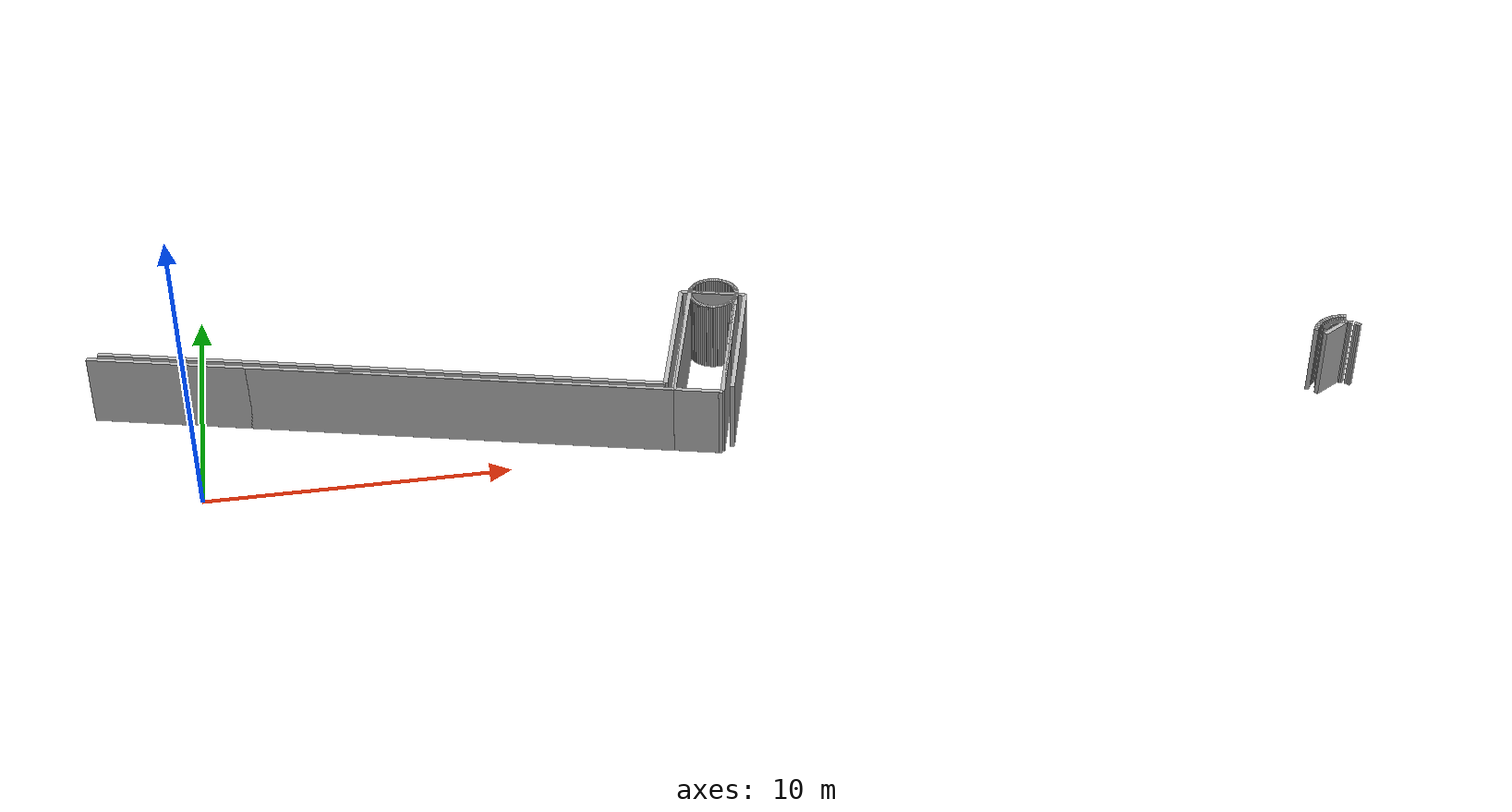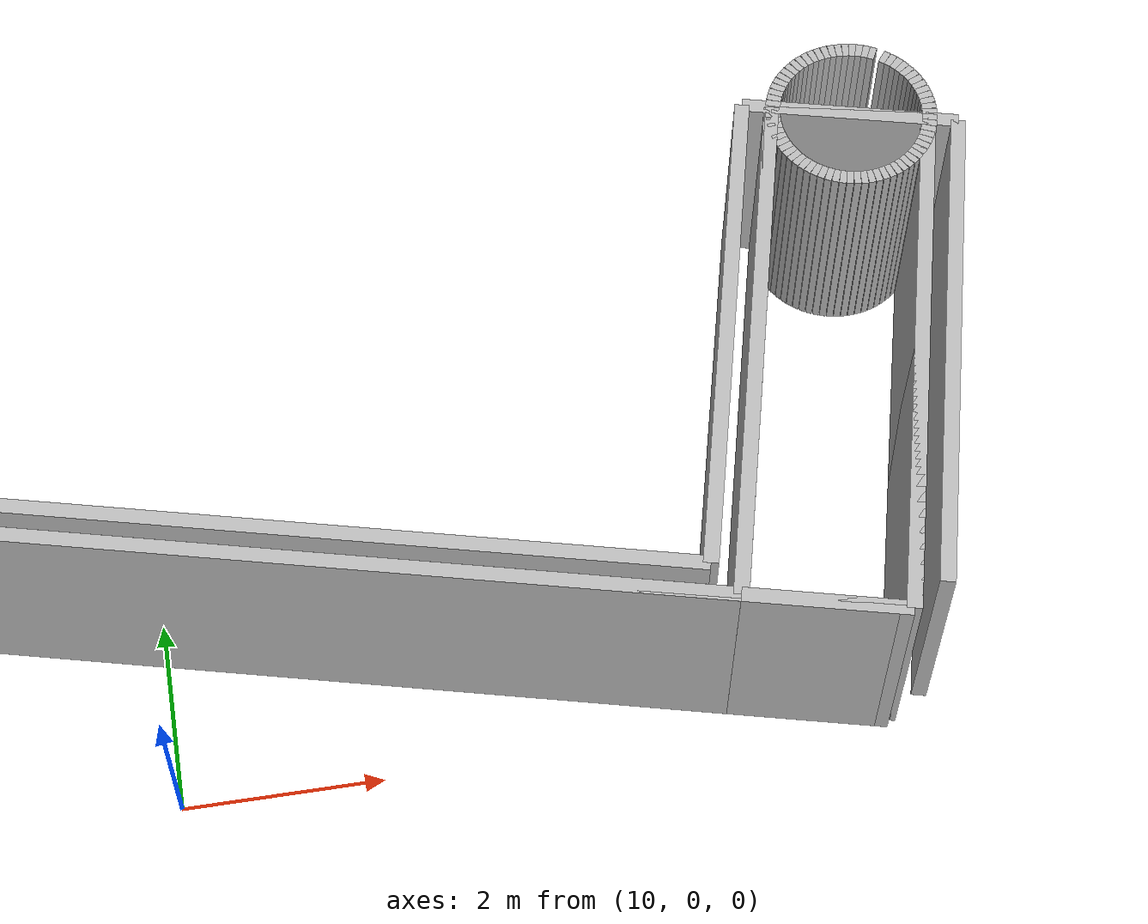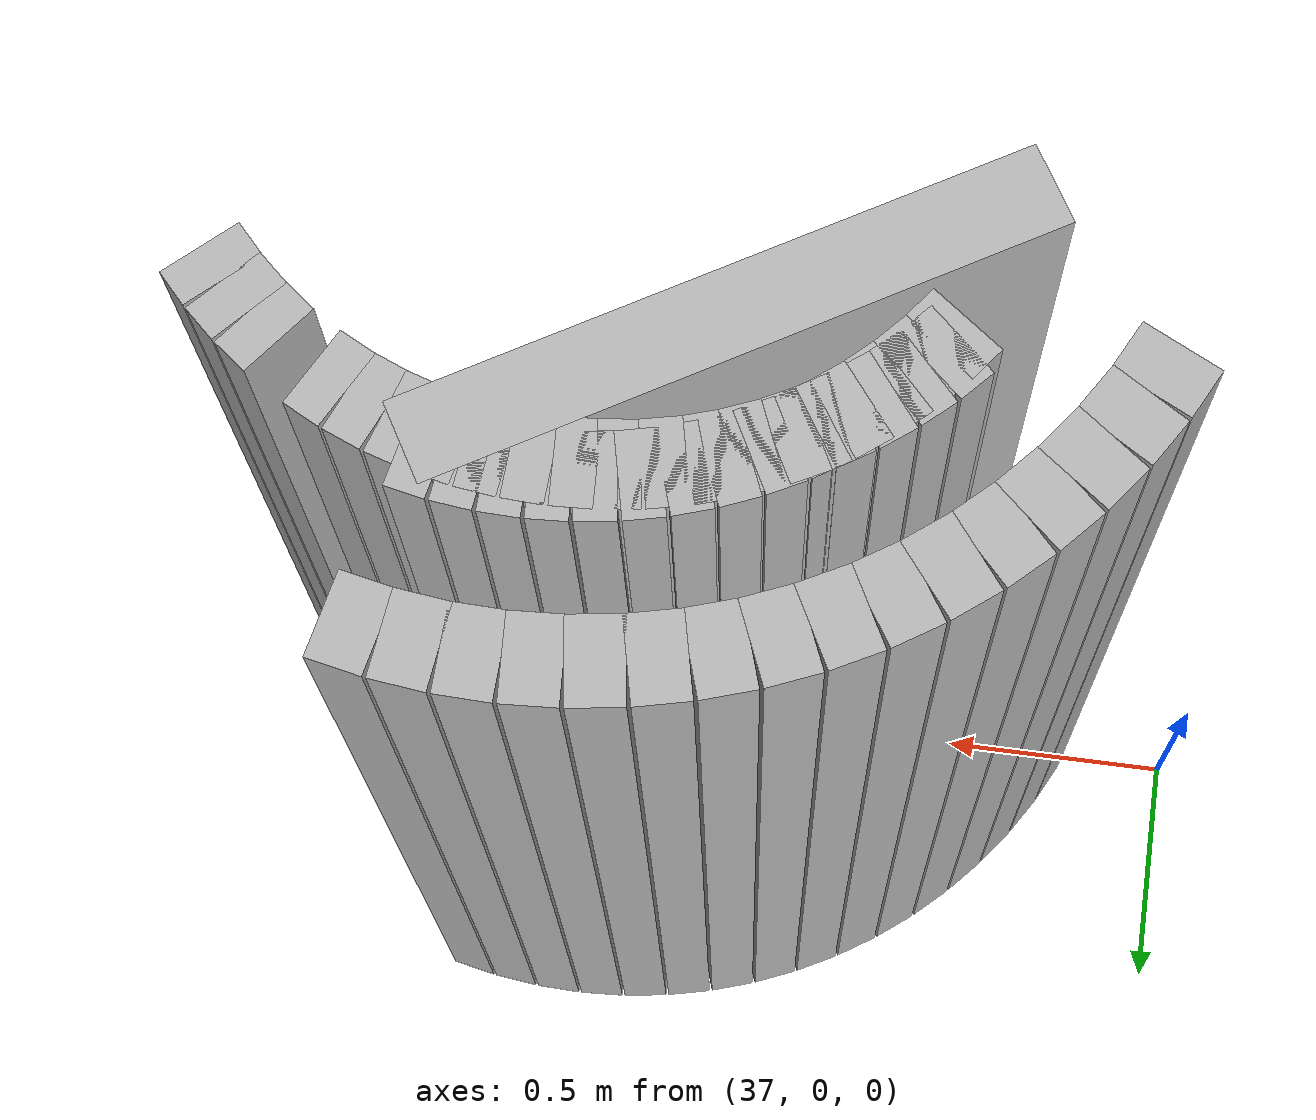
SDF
<?xml version="1.0" ?>
<sdf version="1.6">
  <model name="sps_0308">
    <pose frame="">0 0 0 0 -0 0</pose>
    <static>1</static>
    <self_collide>0</self_collide>
    <allow_auto_disable>0</allow_auto_disable>
    <link name="Wall46">
      <kinematic>0</kinematic>
      <gravity>1</gravity>
      <self_collide>0</self_collide>
      <collision name="collision">
        <geometry>
          <box>
            <size>5.57031 0.15 2.5</size>
          </box>
        </geometry>
        <pose frame="">0 0 0 0 -0 0</pose>
      </collision>
      <visual name="visual">
        <geometry>
          <box>
            <size>5.57031 0.15 2.5</size>
          </box>
        </geometry>
        <pose frame="">0 0 0 0 -0 0</pose>
        <cast_shadows>1</cast_shadows>
        <transparency>0.0</transparency>
      </visual>
      <pose frame="">16.145 2.95302 1.25 0 0 -1.81682</pose>
    </link>
    <link name="Wall431">
      <kinematic>0</kinematic>
      <gravity>1</gravity>
      <self_collide>0</self_collide>
      <collision name="collision">
        <geometry>
          <box>
            <size>2.20035 0.15 2.5</size>
          </box>
        </geometry>
        <pose frame="">0 0 0 0 -0 0</pose>
      </collision>
      <visual name="visual">
        <geometry>
          <box>
            <size>2.20035 0.15 2.5</size>
          </box>
        </geometry>
        <pose frame="">0 0 0 0 -0 0</pose>
        <cast_shadows>1</cast_shadows>
        <transparency>0.0</transparency>
      </visual>
      <pose frame="">17.5995 5.45961 1.25 0 0 -0.245793</pose>
    </link>
    <link name="Wall772">
      <kinematic>0</kinematic>
      <gravity>1</gravity>
      <self_collide>0</self_collide>
      <collision name="collision">
        <geometry>
          <box>
            <size>1.59977 0.15 2.5</size>
          </box>
        </geometry>
        <pose frame="">0 0 0 0 -0 0</pose>
      </collision>
      <visual name="visual">
        <geometry>
          <box>
            <size>1.59977 0.15 2.5</size>
          </box>
        </geometry>
        <pose frame="">0 0 0 0 -0 0</pose>
        <cast_shadows>1</cast_shadows>
        <transparency>0.0</transparency>
      </visual>
      <pose frame="">16.2429 0.0566854 1.25 0 -0 2.89504</pose>
    </link>
    <link name="Wall773">
      <kinematic>0</kinematic>
      <gravity>1</gravity>
      <self_collide>0</self_collide>
      <collision name="collision">
        <geometry>
          <box>
            <size>5.57037 0.15 2.5</size>
          </box>
        </geometry>
        <pose frame="">0 0 0 0 -0 0</pose>
      </collision>
      <visual name="visual">
        <geometry>
          <box>
            <size>5.57037 0.15 2.5</size>
          </box>
        </geometry>
        <pose frame="">0 0 0 0 -0 0</pose>
        <cast_shadows>1</cast_shadows>
        <transparency>0.0</transparency>
      </visual>
      <pose frame="">17.697 2.56279 1.25 0 -0 1.32478</pose>
    </link>
    <link name="Wall774">
      <kinematic>0</kinematic>
      <gravity>1</gravity>
      <self_collide>0</self_collide>
      <collision name="collision">
        <geometry>
          <box>
            <size>5.2705 0.15 2.5</size>
          </box>
        </geometry>
        <pose frame="">0 0 0 0 -0 0</pose>
      </collision>
      <visual name="visual">
        <geometry>
          <box>
            <size>5.2705 0.15 2.5</size>
          </box>
        </geometry>
        <pose frame="">0 0 0 0 -0 0</pose>
        <cast_shadows>1</cast_shadows>
        <transparency>0.0</transparency>
      </visual>
      <pose frame="">18.0249 2.636 1.25 0 -0 1.32478</pose>
    </link>
    <link name="Wall1500">
      <kinematic>0</kinematic>
      <gravity>1</gravity>
      <self_collide>0</self_collide>
      <collision name="collision">
        <geometry>
          <box>
            <size>18.9788 0.15 2.5</size>
          </box>
        </geometry>
        <pose frame="">0 0 0 0 -0 0</pose>
      </collision>
      <visual name="visual">
        <geometry>
          <box>
            <size>18.9788 0.15 2.5</size>
          </box>
        </geometry>
        <pose frame="">0 0 0 0 -0 0</pose>
        <cast_shadows>1</cast_shadows>
        <transparency>0.0</transparency>
      </visual>
      <pose frame="">6.04964 2.94359 1.25 0 -0 2.89373</pose>
    </link>
    <link name="Wall1794">
      <kinematic>0</kinematic>
      <gravity>1</gravity>
      <self_collide>0</self_collide>
      <collision name="collision">
        <geometry>
          <box>
            <size>19.5783 0.15 2.5</size>
          </box>
        </geometry>
        <pose frame="">0 0 0 0 -0 0</pose>
      </collision>
      <visual name="visual">
        <geometry>
          <box>
            <size>19.5783 0.15 2.5</size>
          </box>
        </geometry>
        <pose frame="">0 0 0 0 -0 0</pose>
        <cast_shadows>1</cast_shadows>
        <transparency>0.0</transparency>
      </visual>
      <pose frame="">5.97655 2.65291 1.25 0 -0 2.89377</pose>
    </link>
    <link name="Wall1795">
      <kinematic>0</kinematic>
      <gravity>1</gravity>
      <self_collide>0</self_collide>
      <collision name="collision">
        <geometry>
          <box>
            <size>5.27046 0.15 2.5</size>
          </box>
        </geometry>
        <pose frame="">0 0 0 0 -0 0</pose>
      </collision>
      <visual name="visual">
        <geometry>
          <box>
            <size>5.27046 0.15 2.5</size>
          </box>
        </geometry>
        <pose frame="">0 0 0 0 -0 0</pose>
        <cast_shadows>1</cast_shadows>
        <transparency>0.0</transparency>
      </visual>
      <pose frame="">15.8907 3.1714 1.25 0 0 -1.81677</pose>
    </link>
    <link name="Wall2518">
      <kinematic>0</kinematic>
      <gravity>1</gravity>
      <self_collide>0</self_collide>
      <collision name="collision">
        <geometry>
          <box>
            <size>1.6003 0.15 2.5</size>
          </box>
        </geometry>
        <pose frame="">0 0 0 0 -0 0</pose>
      </collision>
      <visual name="visual">
        <geometry>
          <box>
            <size>1.6003 0.15 2.5</size>
          </box>
        </geometry>
        <pose frame="">0 0 0 0 -0 0</pose>
        <cast_shadows>1</cast_shadows>
        <transparency>0.0</transparency>
      </visual>
      <pose frame="">17.5993 5.45921 1.25 0 0 -0.246311</pose>
    </link>
    <link name="Wall3565">
      <kinematic>0</kinematic>
      <gravity>1</gravity>
      <self_collide>0</self_collide>
      <collision name="collision">
        <geometry>
          <box>
            <size>0.0697539 0.15 2.5</size>
          </box>
        </geometry>
        <pose frame="">0 0 0 0 -0 0</pose>
      </collision>
      <visual name="visual">
        <geometry>
          <box>
            <size>0.0697539 0.15 2.5</size>
          </box>
        </geometry>
        <pose frame="">0 0 0 0 -0 0</pose>
        <cast_shadows>1</cast_shadows>
        <transparency>0.0</transparency>
      </visual>
      <pose frame="">18.0977 6.0901 1.25 0 0 -0.652601</pose>
    </link>
    <link name="Wall3566">
      <kinematic>0</kinematic>
      <gravity>1</gravity>
      <self_collide>0</self_collide>
      <collision name="collision">
        <geometry>
          <box>
            <size>0.0698056 0.15 2.5</size>
          </box>
        </geometry>
        <pose frame="">0 0 0 0 -0 0</pose>
      </collision>
      <visual name="visual">
        <geometry>
          <box>
            <size>0.0698056 0.15 2.5</size>
          </box>
        </geometry>
        <pose frame="">0 0 0 0 -0 0</pose>
        <cast_shadows>1</cast_shadows>
        <transparency>0.0</transparency>
      </visual>
      <pose frame="">18.1511 6.0453 1.25 0 0 -0.743344</pose>
    </link>
    <link name="Wall3567">
      <kinematic>0</kinematic>
      <gravity>1</gravity>
      <self_collide>0</self_collide>
      <collision name="collision">
        <geometry>
          <box>
            <size>0.0698056 0.15 2.5</size>
          </box>
        </geometry>
        <pose frame="">0 0 0 0 -0 0</pose>
      </collision>
      <visual name="visual">
        <geometry>
          <box>
            <size>0.0698056 0.15 2.5</size>
          </box>
        </geometry>
        <pose frame="">0 0 0 0 -0 0</pose>
        <cast_shadows>1</cast_shadows>
        <transparency>0.0</transparency>
      </visual>
      <pose frame="">18.2005 5.99599 1.25 0 0 -0.827453</pose>
    </link>
    <link name="Wall3568">
      <kinematic>0</kinematic>
      <gravity>1</gravity>
      <self_collide>0</self_collide>
      <collision name="collision">
        <geometry>
          <box>
            <size>0.0697539 0.15 2.5</size>
          </box>
        </geometry>
        <pose frame="">0 0 0 0 -0 0</pose>
      </collision>
      <visual name="visual">
        <geometry>
          <box>
            <size>0.0697539 0.15 2.5</size>
          </box>
        </geometry>
        <pose frame="">0 0 0 0 -0 0</pose>
        <cast_shadows>1</cast_shadows>
        <transparency>0.0</transparency>
      </visual>
      <pose frame="">18.2453 5.94258 1.25 0 0 -0.918195</pose>
    </link>
    <link name="Wall3569">
      <kinematic>0</kinematic>
      <gravity>1</gravity>
      <self_collide>0</self_collide>
      <collision name="collision">
        <geometry>
          <box>
            <size>0.0698293 0.15 2.5</size>
          </box>
        </geometry>
        <pose frame="">0 0 0 0 -0 0</pose>
      </collision>
      <visual name="visual">
        <geometry>
          <box>
            <size>0.0698293 0.15 2.5</size>
          </box>
        </geometry>
        <pose frame="">0 0 0 0 -0 0</pose>
        <cast_shadows>1</cast_shadows>
        <transparency>0.0</transparency>
      </visual>
      <pose frame="">18.2851 5.88539 1.25 0 0 -1.00534</pose>
    </link>
    <link name="Wall3570">
      <kinematic>0</kinematic>
      <gravity>1</gravity>
      <self_collide>0</self_collide>
      <collision name="collision">
        <geometry>
          <box>
            <size>0.0697232 0.15 2.5</size>
          </box>
        </geometry>
        <pose frame="">0 0 0 0 -0 0</pose>
      </collision>
      <visual name="visual">
        <geometry>
          <box>
            <size>0.0697232 0.15 2.5</size>
          </box>
        </geometry>
        <pose frame="">0 0 0 0 -0 0</pose>
        <cast_shadows>1</cast_shadows>
        <transparency>0.0</transparency>
      </visual>
      <pose frame="">18.32 5.825 1.25 0 0 -1.09031</pose>
    </link>
    <link name="Wall3571">
      <kinematic>0</kinematic>
      <gravity>1</gravity>
      <self_collide>0</self_collide>
      <collision name="collision">
        <geometry>
          <box>
            <size>0.0697444 0.15 2.5</size>
          </box>
        </geometry>
        <pose frame="">0 0 0 0 -0 0</pose>
      </collision>
      <visual name="visual">
        <geometry>
          <box>
            <size>0.0697444 0.15 2.5</size>
          </box>
        </geometry>
        <pose frame="">0 0 0 0 -0 0</pose>
        <cast_shadows>1</cast_shadows>
        <transparency>0.0</transparency>
      </visual>
      <pose frame="">18.3495 5.76189 1.25 0 0 -1.17648</pose>
    </link>
    <link name="Wall3572">
      <kinematic>0</kinematic>
      <gravity>1</gravity>
      <self_collide>0</self_collide>
      <collision name="collision">
        <geometry>
          <box>
            <size>0.069821 0.15 2.5</size>
          </box>
        </geometry>
        <pose frame="">0 0 0 0 -0 0</pose>
      </collision>
      <visual name="visual">
        <geometry>
          <box>
            <size>0.069821 0.15 2.5</size>
          </box>
        </geometry>
        <pose frame="">0 0 0 0 -0 0</pose>
        <cast_shadows>1</cast_shadows>
        <transparency>0.0</transparency>
      </visual>
      <pose frame="">18.3734 5.69639 1.25 0 0 -1.26536</pose>
    </link>
    <link name="Wall3573">
      <kinematic>0</kinematic>
      <gravity>1</gravity>
      <self_collide>0</self_collide>
      <collision name="collision">
        <geometry>
          <box>
            <size>0.0698566 0.15 2.5</size>
          </box>
        </geometry>
        <pose frame="">0 0 0 0 -0 0</pose>
      </collision>
      <visual name="visual">
        <geometry>
          <box>
            <size>0.0698566 0.15 2.5</size>
          </box>
        </geometry>
        <pose frame="">0 0 0 0 -0 0</pose>
        <cast_shadows>1</cast_shadows>
        <transparency>0.0</transparency>
      </visual>
      <pose frame="">18.3913 5.62898 1.25 0 0 -1.35507</pose>
    </link>
    <link name="Wall3574">
      <kinematic>0</kinematic>
      <gravity>1</gravity>
      <self_collide>0</self_collide>
      <collision name="collision">
        <geometry>
          <box>
            <size>0.0697643 0.15 2.5</size>
          </box>
        </geometry>
        <pose frame="">0 0 0 0 -0 0</pose>
      </collision>
      <visual name="visual">
        <geometry>
          <box>
            <size>0.0697643 0.15 2.5</size>
          </box>
        </geometry>
        <pose frame="">0 0 0 0 -0 0</pose>
        <cast_shadows>1</cast_shadows>
        <transparency>0.0</transparency>
      </visual>
      <pose frame="">18.4034 5.56029 1.25 0 0 -1.4383</pose>
    </link>
    <link name="Wall3575">
      <kinematic>0</kinematic>
      <gravity>1</gravity>
      <self_collide>0</self_collide>
      <collision name="collision">
        <geometry>
          <box>
            <size>0.0698882 0.15 2.5</size>
          </box>
        </geometry>
        <pose frame="">0 0 0 0 -0 0</pose>
      </collision>
      <visual name="visual">
        <geometry>
          <box>
            <size>0.0698882 0.15 2.5</size>
          </box>
        </geometry>
        <pose frame="">0 0 0 0 -0 0</pose>
        <cast_shadows>1</cast_shadows>
        <transparency>0.0</transparency>
      </visual>
      <pose frame="">18.4095 5.4908 1.25 0 0 -1.52799</pose>
    </link>
    <link name="Wall3576">
      <kinematic>0</kinematic>
      <gravity>1</gravity>
      <self_collide>0</self_collide>
      <collision name="collision">
        <geometry>
          <box>
            <size>0.0696524 0.15 2.5</size>
          </box>
        </geometry>
        <pose frame="">0 0 0 0 -0 0</pose>
      </collision>
      <visual name="visual">
        <geometry>
          <box>
            <size>0.0696524 0.15 2.5</size>
          </box>
        </geometry>
        <pose frame="">0 0 0 0 -0 0</pose>
        <cast_shadows>1</cast_shadows>
        <transparency>0.0</transparency>
      </visual>
      <pose frame="">18.4094 5.4211 1.25 0 0 -1.61638</pose>
    </link>
    <link name="Wall3577">
      <kinematic>0</kinematic>
      <gravity>1</gravity>
      <self_collide>0</self_collide>
      <collision name="collision">
        <geometry>
          <box>
            <size>0.0698008 0.15 2.5</size>
          </box>
        </geometry>
        <pose frame="">0 0 0 0 -0 0</pose>
      </collision>
      <visual name="visual">
        <geometry>
          <box>
            <size>0.0698008 0.15 2.5</size>
          </box>
        </geometry>
        <pose frame="">0 0 0 0 -0 0</pose>
        <cast_shadows>1</cast_shadows>
        <transparency>0.0</transparency>
      </visual>
      <pose frame="">18.4033 5.3517 1.25 0 0 -1.70057</pose>
    </link>
    <link name="Wall3578">
      <kinematic>0</kinematic>
      <gravity>1</gravity>
      <self_collide>0</self_collide>
      <collision name="collision">
        <geometry>
          <box>
            <size>0.0698497 0.15 2.5</size>
          </box>
        </geometry>
        <pose frame="">0 0 0 0 -0 0</pose>
      </collision>
      <visual name="visual">
        <geometry>
          <box>
            <size>0.0698497 0.15 2.5</size>
          </box>
        </geometry>
        <pose frame="">0 0 0 0 -0 0</pose>
        <cast_shadows>1</cast_shadows>
        <transparency>0.0</transparency>
      </visual>
      <pose frame="">18.3912 5.283 1.25 0 0 -1.79013</pose>
    </link>
    <link name="Wall3579">
      <kinematic>0</kinematic>
      <gravity>1</gravity>
      <self_collide>0</self_collide>
      <collision name="collision">
        <geometry>
          <box>
            <size>0.0698793 0.15 2.5</size>
          </box>
        </geometry>
        <pose frame="">0 0 0 0 -0 0</pose>
      </collision>
      <visual name="visual">
        <geometry>
          <box>
            <size>0.0698793 0.15 2.5</size>
          </box>
        </geometry>
        <pose frame="">0 0 0 0 -0 0</pose>
        <cast_shadows>1</cast_shadows>
        <transparency>0.0</transparency>
      </visual>
      <pose frame="">18.3731 5.21559 1.25 0 0 -1.87597</pose>
    </link>
    <link name="Wall3580">
      <kinematic>0</kinematic>
      <gravity>1</gravity>
      <self_collide>0</self_collide>
      <collision name="collision">
        <geometry>
          <box>
            <size>0.0697444 0.15 2.5</size>
          </box>
        </geometry>
        <pose frame="">0 0 0 0 -0 0</pose>
      </collision>
      <visual name="visual">
        <geometry>
          <box>
            <size>0.0697444 0.15 2.5</size>
          </box>
        </geometry>
        <pose frame="">0 0 0 0 -0 0</pose>
        <cast_shadows>1</cast_shadows>
        <transparency>0.0</transparency>
      </visual>
      <pose frame="">18.3492 5.15007 1.25 0 0 -1.96512</pose>
    </link>
    <link name="Wall3581">
      <kinematic>0</kinematic>
      <gravity>1</gravity>
      <self_collide>0</self_collide>
      <collision name="collision">
        <geometry>
          <box>
            <size>0.0698034 0.15 2.5</size>
          </box>
        </geometry>
        <pose frame="">0 0 0 0 -0 0</pose>
      </collision>
      <visual name="visual">
        <geometry>
          <box>
            <size>0.0698034 0.15 2.5</size>
          </box>
        </geometry>
        <pose frame="">0 0 0 0 -0 0</pose>
        <cast_shadows>1</cast_shadows>
        <transparency>0.0</transparency>
      </visual>
      <pose frame="">18.3198 5.0869 1.25 0 0 -2.0497</pose>
    </link>
    <link name="Wall3582">
      <kinematic>0</kinematic>
      <gravity>1</gravity>
      <self_collide>0</self_collide>
      <collision name="collision">
        <geometry>
          <box>
            <size>0.0697262 0.15 2.5</size>
          </box>
        </geometry>
        <pose frame="">0 0 0 0 -0 0</pose>
      </collision>
      <visual name="visual">
        <geometry>
          <box>
            <size>0.0697262 0.15 2.5</size>
          </box>
        </geometry>
        <pose frame="">0 0 0 0 -0 0</pose>
        <cast_shadows>1</cast_shadows>
        <transparency>0.0</transparency>
      </visual>
      <pose frame="">18.285 5.0265 1.25 0 0 -2.13719</pose>
    </link>
    <link name="Wall3583">
      <kinematic>0</kinematic>
      <gravity>1</gravity>
      <self_collide>0</self_collide>
      <collision name="collision">
        <geometry>
          <box>
            <size>0.0699024 0.15 2.5</size>
          </box>
        </geometry>
        <pose frame="">0 0 0 0 -0 0</pose>
      </collision>
      <visual name="visual">
        <geometry>
          <box>
            <size>0.0699024 0.15 2.5</size>
          </box>
        </geometry>
        <pose frame="">0 0 0 0 -0 0</pose>
        <cast_shadows>1</cast_shadows>
        <transparency>0.0</transparency>
      </visual>
      <pose frame="">18.245 4.96937 1.25 0 0 -2.22617</pose>
    </link>
    <link name="Wall3584">
      <kinematic>0</kinematic>
      <gravity>1</gravity>
      <self_collide>0</self_collide>
      <collision name="collision">
        <geometry>
          <box>
            <size>0.0697644 0.15 2.5</size>
          </box>
        </geometry>
        <pose frame="">0 0 0 0 -0 0</pose>
      </collision>
      <visual name="visual">
        <geometry>
          <box>
            <size>0.0697644 0.15 2.5</size>
          </box>
        </geometry>
        <pose frame="">0 0 0 0 -0 0</pose>
        <cast_shadows>1</cast_shadows>
        <transparency>0.0</transparency>
      </visual>
      <pose frame="">18.2001 4.91597 1.25 0 0 -2.3135</pose>
    </link>
    <link name="Wall3585">
      <kinematic>0</kinematic>
      <gravity>1</gravity>
      <self_collide>0</self_collide>
      <collision name="collision">
        <geometry>
          <box>
            <size>0.0696407 0.15 2.5</size>
          </box>
        </geometry>
        <pose frame="">0 0 0 0 -0 0</pose>
      </collision>
      <visual name="visual">
        <geometry>
          <box>
            <size>0.0696407 0.15 2.5</size>
          </box>
        </geometry>
        <pose frame="">0 0 0 0 -0 0</pose>
        <cast_shadows>1</cast_shadows>
        <transparency>0.0</transparency>
      </visual>
      <pose frame="">18.1508 4.86677 1.25 0 0 -2.40083</pose>
    </link>
    <link name="Wall3586">
      <kinematic>0</kinematic>
      <gravity>1</gravity>
      <self_collide>0</self_collide>
      <collision name="collision">
        <geometry>
          <box>
            <size>0.0699024 0.15 2.5</size>
          </box>
        </geometry>
        <pose frame="">0 0 0 0 -0 0</pose>
      </collision>
      <visual name="visual">
        <geometry>
          <box>
            <size>0.0699024 0.15 2.5</size>
          </box>
        </geometry>
        <pose frame="">0 0 0 0 -0 0</pose>
        <cast_shadows>1</cast_shadows>
        <transparency>0.0</transparency>
      </visual>
      <pose frame="">18.0974 4.82197 1.25 0 0 -2.48622</pose>
    </link>
    <link name="Wall3587">
      <kinematic>0</kinematic>
      <gravity>1</gravity>
      <self_collide>0</self_collide>
      <collision name="collision">
        <geometry>
          <box>
            <size>0.0696935 0.15 2.5</size>
          </box>
        </geometry>
        <pose frame="">0 0 0 0 -0 0</pose>
      </collision>
      <visual name="visual">
        <geometry>
          <box>
            <size>0.0696935 0.15 2.5</size>
          </box>
        </geometry>
        <pose frame="">0 0 0 0 -0 0</pose>
        <cast_shadows>1</cast_shadows>
        <transparency>0.0</transparency>
      </visual>
      <pose frame="">18.0402 4.782 1.25 0 0 -2.57594</pose>
    </link>
    <link name="Wall3588">
      <kinematic>0</kinematic>
      <gravity>1</gravity>
      <self_collide>0</self_collide>
      <collision name="collision">
        <geometry>
          <box>
            <size>0.0698315 0.15 2.5</size>
          </box>
        </geometry>
        <pose frame="">0 0 0 0 -0 0</pose>
      </collision>
      <visual name="visual">
        <geometry>
          <box>
            <size>0.0698315 0.15 2.5</size>
          </box>
        </geometry>
        <pose frame="">0 0 0 0 -0 0</pose>
        <cast_shadows>1</cast_shadows>
        <transparency>0.0</transparency>
      </visual>
      <pose frame="">17.9799 4.74721 1.25 0 0 -2.66192</pose>
    </link>
    <link name="Wall3589">
      <kinematic>0</kinematic>
      <gravity>1</gravity>
      <self_collide>0</self_collide>
      <collision name="collision">
        <geometry>
          <box>
            <size>0.0697444 0.15 2.5</size>
          </box>
        </geometry>
        <pose frame="">0 0 0 0 -0 0</pose>
      </collision>
      <visual name="visual">
        <geometry>
          <box>
            <size>0.0697444 0.15 2.5</size>
          </box>
        </geometry>
        <pose frame="">0 0 0 0 -0 0</pose>
        <cast_shadows>1</cast_shadows>
        <transparency>0.0</transparency>
      </visual>
      <pose frame="">17.9167 4.7177 1.25 0 0 -2.74727</pose>
    </link>
    <link name="Wall3590">
      <kinematic>0</kinematic>
      <gravity>1</gravity>
      <self_collide>0</self_collide>
      <collision name="collision">
        <geometry>
          <box>
            <size>0.0698245 0.15 2.5</size>
          </box>
        </geometry>
        <pose frame="">0 0 0 0 -0 0</pose>
      </collision>
      <visual name="visual">
        <geometry>
          <box>
            <size>0.0698245 0.15 2.5</size>
          </box>
        </geometry>
        <pose frame="">0 0 0 0 -0 0</pose>
        <cast_shadows>1</cast_shadows>
        <transparency>0.0</transparency>
      </visual>
      <pose frame="">17.8512 4.69389 1.25 0 0 -2.83892</pose>
    </link>
    <link name="Wall3591">
      <kinematic>0</kinematic>
      <gravity>1</gravity>
      <self_collide>0</self_collide>
      <collision name="collision">
        <geometry>
          <box>
            <size>0.0698497 0.15 2.5</size>
          </box>
        </geometry>
        <pose frame="">0 0 0 0 -0 0</pose>
      </collision>
      <visual name="visual">
        <geometry>
          <box>
            <size>0.0698497 0.15 2.5</size>
          </box>
        </geometry>
        <pose frame="">0 0 0 0 -0 0</pose>
        <cast_shadows>1</cast_shadows>
        <transparency>0.0</transparency>
      </visual>
      <pose frame="">17.7837 4.67589 1.25 0 0 -2.92226</pose>
    </link>
    <link name="Wall3592">
      <kinematic>0</kinematic>
      <gravity>1</gravity>
      <self_collide>0</self_collide>
      <collision name="collision">
        <geometry>
          <box>
            <size>0.069793 0.15 2.5</size>
          </box>
        </geometry>
        <pose frame="">0 0 0 0 -0 0</pose>
      </collision>
      <visual name="visual">
        <geometry>
          <box>
            <size>0.069793 0.15 2.5</size>
          </box>
        </geometry>
        <pose frame="">0 0 0 0 -0 0</pose>
        <cast_shadows>1</cast_shadows>
        <transparency>0.0</transparency>
      </visual>
      <pose frame="">17.715 4.6638 1.25 0 0 -3.01268</pose>
    </link>
    <link name="Wall3593">
      <kinematic>0</kinematic>
      <gravity>1</gravity>
      <self_collide>0</self_collide>
      <collision name="collision">
        <geometry>
          <box>
            <size>0.0696552 0.15 2.5</size>
          </box>
        </geometry>
        <pose frame="">0 0 0 0 -0 0</pose>
      </collision>
      <visual name="visual">
        <geometry>
          <box>
            <size>0.0696552 0.15 2.5</size>
          </box>
        </geometry>
        <pose frame="">0 0 0 0 -0 0</pose>
        <cast_shadows>1</cast_shadows>
        <transparency>0.0</transparency>
      </visual>
      <pose frame="">17.6457 4.6577 1.25 0 0 -3.09513</pose>
    </link>
    <link name="Wall3594">
      <kinematic>0</kinematic>
      <gravity>1</gravity>
      <self_collide>0</self_collide>
      <collision name="collision">
        <geometry>
          <box>
            <size>0.0698991 0.15 2.5</size>
          </box>
        </geometry>
        <pose frame="">0 0 0 0 -0 0</pose>
      </collision>
      <visual name="visual">
        <geometry>
          <box>
            <size>0.0698991 0.15 2.5</size>
          </box>
        </geometry>
        <pose frame="">0 0 0 0 -0 0</pose>
        <cast_shadows>1</cast_shadows>
        <transparency>0.0</transparency>
      </visual>
      <pose frame="">17.5759 4.6577 1.25 0 -0 3.0953</pose>
    </link>
    <link name="Wall3595">
      <kinematic>0</kinematic>
      <gravity>1</gravity>
      <self_collide>0</self_collide>
      <collision name="collision">
        <geometry>
          <box>
            <size>0.0697562 0.15 2.5</size>
          </box>
        </geometry>
        <pose frame="">0 0 0 0 -0 0</pose>
      </collision>
      <visual name="visual">
        <geometry>
          <box>
            <size>0.0697562 0.15 2.5</size>
          </box>
        </geometry>
        <pose frame="">0 0 0 0 -0 0</pose>
        <cast_shadows>1</cast_shadows>
        <transparency>0.0</transparency>
      </visual>
      <pose frame="">17.5065 4.66389 1.25 0 -0 3.00997</pose>
    </link>
    <link name="Wall3596">
      <kinematic>0</kinematic>
      <gravity>1</gravity>
      <self_collide>0</self_collide>
      <collision name="collision">
        <geometry>
          <box>
            <size>0.0696908 0.15 2.5</size>
          </box>
        </geometry>
        <pose frame="">0 0 0 0 -0 0</pose>
      </collision>
      <visual name="visual">
        <geometry>
          <box>
            <size>0.0696908 0.15 2.5</size>
          </box>
        </geometry>
        <pose frame="">0 0 0 0 -0 0</pose>
        <cast_shadows>1</cast_shadows>
        <transparency>0.0</transparency>
      </visual>
      <pose frame="">17.4379 4.67598 1.25 0 -0 2.92444</pose>
    </link>
    <link name="Wall3597">
      <kinematic>0</kinematic>
      <gravity>1</gravity>
      <self_collide>0</self_collide>
      <collision name="collision">
        <geometry>
          <box>
            <size>0.069821 0.15 2.5</size>
          </box>
        </geometry>
        <pose frame="">0 0 0 0 -0 0</pose>
      </collision>
      <visual name="visual">
        <geometry>
          <box>
            <size>0.069821 0.15 2.5</size>
          </box>
        </geometry>
        <pose frame="">0 0 0 0 -0 0</pose>
        <cast_shadows>1</cast_shadows>
        <transparency>0.0</transparency>
      </visual>
      <pose frame="">17.3705 4.69398 1.25 0 -0 2.83615</pose>
    </link>
    <link name="Wall3598">
      <kinematic>0</kinematic>
      <gravity>1</gravity>
      <self_collide>0</self_collide>
      <collision name="collision">
        <geometry>
          <box>
            <size>0.0699135 0.15 2.5</size>
          </box>
        </geometry>
        <pose frame="">0 0 0 0 -0 0</pose>
      </collision>
      <visual name="visual">
        <geometry>
          <box>
            <size>0.0699135 0.15 2.5</size>
          </box>
        </geometry>
        <pose frame="">0 0 0 0 -0 0</pose>
        <cast_shadows>1</cast_shadows>
        <transparency>0.0</transparency>
      </visual>
      <pose frame="">17.305 4.71788 1.25 0 -0 2.74828</pose>
    </link>
    <link name="Wall3599">
      <kinematic>0</kinematic>
      <gravity>1</gravity>
      <self_collide>0</self_collide>
      <collision name="collision">
        <geometry>
          <box>
            <size>0.0697232 0.15 2.5</size>
          </box>
        </geometry>
        <pose frame="">0 0 0 0 -0 0</pose>
      </collision>
      <visual name="visual">
        <geometry>
          <box>
            <size>0.0697232 0.15 2.5</size>
          </box>
        </geometry>
        <pose frame="">0 0 0 0 -0 0</pose>
        <cast_shadows>1</cast_shadows>
        <transparency>0.0</transparency>
      </visual>
      <pose frame="">17.2418 4.74739 1.25 0 -0 2.66111</pose>
    </link>
    <link name="Wall3600">
      <kinematic>0</kinematic>
      <gravity>1</gravity>
      <self_collide>0</self_collide>
      <collision name="collision">
        <geometry>
          <box>
            <size>0.0697732 0.15 2.5</size>
          </box>
        </geometry>
        <pose frame="">0 0 0 0 -0 0</pose>
      </collision>
      <visual name="visual">
        <geometry>
          <box>
            <size>0.0697732 0.15 2.5</size>
          </box>
        </geometry>
        <pose frame="">0 0 0 0 -0 0</pose>
        <cast_shadows>1</cast_shadows>
        <transparency>0.0</transparency>
      </visual>
      <pose frame="">17.1814 4.7823 1.25 0 -0 2.57252</pose>
    </link>
    <link name="Wall3601">
      <kinematic>0</kinematic>
      <gravity>1</gravity>
      <self_collide>0</self_collide>
      <collision name="collision">
        <geometry>
          <box>
            <size>0.0697909 0.15 2.5</size>
          </box>
        </geometry>
        <pose frame="">0 0 0 0 -0 0</pose>
      </collision>
      <visual name="visual">
        <geometry>
          <box>
            <size>0.0697909 0.15 2.5</size>
          </box>
        </geometry>
        <pose frame="">0 0 0 0 -0 0</pose>
        <cast_shadows>1</cast_shadows>
        <transparency>0.0</transparency>
      </visual>
      <pose frame="">17.1244 4.82231 1.25 0 -0 2.4883</pose>
    </link>
    <link name="Wall3602">
      <kinematic>0</kinematic>
      <gravity>1</gravity>
      <self_collide>0</self_collide>
      <collision name="collision">
        <geometry>
          <box>
            <size>0.0697644 0.15 2.5</size>
          </box>
        </geometry>
        <pose frame="">0 0 0 0 -0 0</pose>
      </collision>
      <visual name="visual">
        <geometry>
          <box>
            <size>0.0697644 0.15 2.5</size>
          </box>
        </geometry>
        <pose frame="">0 0 0 0 -0 0</pose>
        <cast_shadows>1</cast_shadows>
        <transparency>0.0</transparency>
      </visual>
      <pose frame="">17.0709 4.86711 1.25 0 -0 2.39889</pose>
    </link>
    <link name="Wall3603">
      <kinematic>0</kinematic>
      <gravity>1</gravity>
      <self_collide>0</self_collide>
      <collision name="collision">
        <geometry>
          <box>
            <size>0.0697644 0.15 2.5</size>
          </box>
        </geometry>
        <pose frame="">0 0 0 0 -0 0</pose>
      </collision>
      <visual name="visual">
        <geometry>
          <box>
            <size>0.0697644 0.15 2.5</size>
          </box>
        </geometry>
        <pose frame="">0 0 0 0 -0 0</pose>
        <cast_shadows>1</cast_shadows>
        <transparency>0.0</transparency>
      </visual>
      <pose frame="">17.0217 4.9164 1.25 0 -0 2.3135</pose>
    </link>
    <link name="Wall3604">
      <kinematic>0</kinematic>
      <gravity>1</gravity>
      <self_collide>0</self_collide>
      <collision name="collision">
        <geometry>
          <box>
            <size>0.0697909 0.15 2.5</size>
          </box>
        </geometry>
        <pose frame="">0 0 0 0 -0 0</pose>
      </collision>
      <visual name="visual">
        <geometry>
          <box>
            <size>0.0697909 0.15 2.5</size>
          </box>
        </geometry>
        <pose frame="">0 0 0 0 -0 0</pose>
        <cast_shadows>1</cast_shadows>
        <transparency>0.0</transparency>
      </visual>
      <pose frame="">16.9769 4.9698 1.25 0 -0 2.22409</pose>
    </link>
    <link name="Wall3605">
      <kinematic>0</kinematic>
      <gravity>1</gravity>
      <self_collide>0</self_collide>
      <collision name="collision">
        <geometry>
          <box>
            <size>0.0699275 0.15 2.5</size>
          </box>
        </geometry>
        <pose frame="">0 0 0 0 -0 0</pose>
      </collision>
      <visual name="visual">
        <geometry>
          <box>
            <size>0.0699275 0.15 2.5</size>
          </box>
        </geometry>
        <pose frame="">0 0 0 0 -0 0</pose>
        <cast_shadows>1</cast_shadows>
        <transparency>0.0</transparency>
      </visual>
      <pose frame="">16.9369 5.02699 1.25 0 -0 2.13846</pose>
    </link>
    <link name="Wall3606">
      <kinematic>0</kinematic>
      <gravity>1</gravity>
      <self_collide>0</self_collide>
      <collision name="collision">
        <geometry>
          <box>
            <size>0.0697232 0.15 2.5</size>
          </box>
        </geometry>
        <pose frame="">0 0 0 0 -0 0</pose>
      </collision>
      <visual name="visual">
        <geometry>
          <box>
            <size>0.0697232 0.15 2.5</size>
          </box>
        </geometry>
        <pose frame="">0 0 0 0 -0 0</pose>
        <cast_shadows>1</cast_shadows>
        <transparency>0.0</transparency>
      </visual>
      <pose frame="">16.9019 5.08739 1.25 0 -0 2.05128</pose>
    </link>
    <link name="Wall3607">
      <kinematic>0</kinematic>
      <gravity>1</gravity>
      <self_collide>0</self_collide>
      <collision name="collision">
        <geometry>
          <box>
            <size>0.0698203 0.15 2.5</size>
          </box>
        </geometry>
        <pose frame="">0 0 0 0 -0 0</pose>
      </collision>
      <visual name="visual">
        <geometry>
          <box>
            <size>0.0698203 0.15 2.5</size>
          </box>
        </geometry>
        <pose frame="">0 0 0 0 -0 0</pose>
        <cast_shadows>1</cast_shadows>
        <transparency>0.0</transparency>
      </visual>
      <pose frame="">16.8726 5.15059 1.25 0 -0 1.96088</pose>
    </link>
    <link name="Wall3608">
      <kinematic>0</kinematic>
      <gravity>1</gravity>
      <self_collide>0</self_collide>
      <collision name="collision">
        <geometry>
          <box>
            <size>0.0696464 0.15 2.5</size>
          </box>
        </geometry>
        <pose frame="">0 0 0 0 -0 0</pose>
      </collision>
      <visual name="visual">
        <geometry>
          <box>
            <size>0.0696464 0.15 2.5</size>
          </box>
        </geometry>
        <pose frame="">0 0 0 0 -0 0</pose>
        <cast_shadows>1</cast_shadows>
        <transparency>0.0</transparency>
      </visual>
      <pose frame="">16.8488 5.21608 1.25 0 -0 1.87703</pose>
    </link>
    <link name="Wall3609">
      <kinematic>0</kinematic>
      <gravity>1</gravity>
      <self_collide>0</self_collide>
      <collision name="collision">
        <geometry>
          <box>
            <size>0.0699092 0.15 2.5</size>
          </box>
        </geometry>
        <pose frame="">0 0 0 0 -0 0</pose>
      </collision>
      <visual name="visual">
        <geometry>
          <box>
            <size>0.0699092 0.15 2.5</size>
          </box>
        </geometry>
        <pose frame="">0 0 0 0 -0 0</pose>
        <cast_shadows>1</cast_shadows>
        <transparency>0.0</transparency>
      </visual>
      <pose frame="">16.8307 5.2834 1.25 0 -0 1.78994</pose>
    </link>
    <link name="Wall3610">
      <kinematic>0</kinematic>
      <gravity>1</gravity>
      <self_collide>0</self_collide>
      <collision name="collision">
        <geometry>
          <box>
            <size>0.0697403 0.15 2.5</size>
          </box>
        </geometry>
        <pose frame="">0 0 0 0 -0 0</pose>
      </collision>
      <visual name="visual">
        <geometry>
          <box>
            <size>0.0697403 0.15 2.5</size>
          </box>
        </geometry>
        <pose frame="">0 0 0 0 -0 0</pose>
        <cast_shadows>1</cast_shadows>
        <transparency>0.0</transparency>
      </visual>
      <pose frame="">16.8186 5.3521 1.25 0 -0 1.70069</pose>
    </link>
    <link name="Wall3611">
      <kinematic>0</kinematic>
      <gravity>1</gravity>
      <self_collide>0</self_collide>
      <collision name="collision">
        <geometry>
          <box>
            <size>0.0698882 0.15 2.5</size>
          </box>
        </geometry>
        <pose frame="">0 0 0 0 -0 0</pose>
      </collision>
      <visual name="visual">
        <geometry>
          <box>
            <size>0.0698882 0.15 2.5</size>
          </box>
        </geometry>
        <pose frame="">0 0 0 0 -0 0</pose>
        <cast_shadows>1</cast_shadows>
        <transparency>0.0</transparency>
      </visual>
      <pose frame="">16.8126 5.42158 1.25 0 -0 1.6136</pose>
    </link>
    <link name="Wall3612">
      <kinematic>0</kinematic>
      <gravity>1</gravity>
      <self_collide>0</self_collide>
      <collision name="collision">
        <geometry>
          <box>
            <size>0.0696443 0.15 2.5</size>
          </box>
        </geometry>
        <pose frame="">0 0 0 0 -0 0</pose>
      </collision>
      <visual name="visual">
        <geometry>
          <box>
            <size>0.0696443 0.15 2.5</size>
          </box>
        </geometry>
        <pose frame="">0 0 0 0 -0 0</pose>
        <cast_shadows>1</cast_shadows>
        <transparency>0.0</transparency>
      </visual>
      <pose frame="">16.8126 5.49129 1.25 0 -0 1.52784</pose>
    </link>
    <link name="Wall3613">
      <kinematic>0</kinematic>
      <gravity>1</gravity>
      <self_collide>0</self_collide>
      <collision name="collision">
        <geometry>
          <box>
            <size>0.0698248 0.15 2.5</size>
          </box>
        </geometry>
        <pose frame="">0 0 0 0 -0 0</pose>
      </collision>
      <visual name="visual">
        <geometry>
          <box>
            <size>0.0698248 0.15 2.5</size>
          </box>
        </geometry>
        <pose frame="">0 0 0 0 -0 0</pose>
        <cast_shadows>1</cast_shadows>
        <transparency>0.0</transparency>
      </visual>
      <pose frame="">16.8187 5.56068 1.25 0 -0 1.43842</pose>
    </link>
    <link name="Wall3614">
      <kinematic>0</kinematic>
      <gravity>1</gravity>
      <self_collide>0</self_collide>
      <collision name="collision">
        <geometry>
          <box>
            <size>0.0698101 0.15 2.5</size>
          </box>
        </geometry>
        <pose frame="">0 0 0 0 -0 0</pose>
      </collision>
      <visual name="visual">
        <geometry>
          <box>
            <size>0.0698101 0.15 2.5</size>
          </box>
        </geometry>
        <pose frame="">0 0 0 0 -0 0</pose>
        <cast_shadows>1</cast_shadows>
        <transparency>0.0</transparency>
      </visual>
      <pose frame="">16.8308 5.62938 1.25 0 -0 1.35402</pose>
    </link>
    <link name="Wall3615">
      <kinematic>0</kinematic>
      <gravity>1</gravity>
      <self_collide>0</self_collide>
      <collision name="collision">
        <geometry>
          <box>
            <size>0.0698793 0.15 2.5</size>
          </box>
        </geometry>
        <pose frame="">0 0 0 0 -0 0</pose>
      </collision>
      <visual name="visual">
        <geometry>
          <box>
            <size>0.0698793 0.15 2.5</size>
          </box>
        </geometry>
        <pose frame="">0 0 0 0 -0 0</pose>
        <cast_shadows>1</cast_shadows>
        <transparency>0.0</transparency>
      </visual>
      <pose frame="">16.8488 5.69679 1.25 0 -0 1.26562</pose>
    </link>
    <link name="Wall3616">
      <kinematic>0</kinematic>
      <gravity>1</gravity>
      <self_collide>0</self_collide>
      <collision name="collision">
        <geometry>
          <box>
            <size>0.0697444 0.15 2.5</size>
          </box>
        </geometry>
        <pose frame="">0 0 0 0 -0 0</pose>
      </collision>
      <visual name="visual">
        <geometry>
          <box>
            <size>0.0697444 0.15 2.5</size>
          </box>
        </geometry>
        <pose frame="">0 0 0 0 -0 0</pose>
        <cast_shadows>1</cast_shadows>
        <transparency>0.0</transparency>
      </visual>
      <pose frame="">16.8727 5.76231 1.25 0 -0 1.17648</pose>
    </link>
    <link name="Wall3617">
      <kinematic>0</kinematic>
      <gravity>1</gravity>
      <self_collide>0</self_collide>
      <collision name="collision">
        <geometry>
          <box>
            <size>0.0696409 0.15 2.5</size>
          </box>
        </geometry>
        <pose frame="">0 0 0 0 -0 0</pose>
      </collision>
      <visual name="visual">
        <geometry>
          <box>
            <size>0.0696409 0.15 2.5</size>
          </box>
        </geometry>
        <pose frame="">0 0 0 0 -0 0</pose>
        <cast_shadows>1</cast_shadows>
        <transparency>0.0</transparency>
      </visual>
      <pose frame="">16.9022 5.82539 1.25 0 -0 1.09069</pose>
    </link>
    <link name="Wall3618">
      <kinematic>0</kinematic>
      <gravity>1</gravity>
      <self_collide>0</self_collide>
      <collision name="collision">
        <geometry>
          <box>
            <size>0.069979 0.15 2.5</size>
          </box>
        </geometry>
        <pose frame="">0 0 0 0 -0 0</pose>
      </collision>
      <visual name="visual">
        <geometry>
          <box>
            <size>0.069979 0.15 2.5</size>
          </box>
        </geometry>
        <pose frame="">0 0 0 0 -0 0</pose>
        <cast_shadows>1</cast_shadows>
        <transparency>0.0</transparency>
      </visual>
      <pose frame="">16.937 5.88579 1.25 0 -0 1.0036</pose>
    </link>
    <link name="Wall3619">
      <kinematic>0</kinematic>
      <gravity>1</gravity>
      <self_collide>0</self_collide>
      <collision name="collision">
        <geometry>
          <box>
            <size>0.0695972 0.15 2.5</size>
          </box>
        </geometry>
        <pose frame="">0 0 0 0 -0 0</pose>
      </collision>
      <visual name="visual">
        <geometry>
          <box>
            <size>0.0695972 0.15 2.5</size>
          </box>
        </geometry>
        <pose frame="">0 0 0 0 -0 0</pose>
        <cast_shadows>1</cast_shadows>
        <transparency>0.0</transparency>
      </visual>
      <pose frame="">16.977 5.94289 1.25 0 -0 0.915368</pose>
    </link>
    <link name="Wall3620">
      <kinematic>0</kinematic>
      <gravity>1</gravity>
      <self_collide>0</self_collide>
      <collision name="collision">
        <geometry>
          <box>
            <size>0.0699444 0.15 2.5</size>
          </box>
        </geometry>
        <pose frame="">0 0 0 0 -0 0</pose>
      </collision>
      <visual name="visual">
        <geometry>
          <box>
            <size>0.0699444 0.15 2.5</size>
          </box>
        </geometry>
        <pose frame="">0 0 0 0 -0 0</pose>
        <cast_shadows>1</cast_shadows>
        <transparency>0.0</transparency>
      </visual>
      <pose frame="">17.0218 5.99629 1.25 0 -0 0.830457</pose>
    </link>
    <link name="Wall3621">
      <kinematic>0</kinematic>
      <gravity>1</gravity>
      <self_collide>0</self_collide>
      <collision name="collision">
        <geometry>
          <box>
            <size>0.0696857 0.15 2.5</size>
          </box>
        </geometry>
        <pose frame="">0 0 0 0 -0 0</pose>
      </collision>
      <visual name="visual">
        <geometry>
          <box>
            <size>0.0696857 0.15 2.5</size>
          </box>
        </geometry>
        <pose frame="">0 0 0 0 -0 0</pose>
        <cast_shadows>1</cast_shadows>
        <transparency>0.0</transparency>
      </visual>
      <pose frame="">17.0712 6.04561 1.25 0 -0 0.740172</pose>
    </link>
    <link name="Wall3622">
      <kinematic>0</kinematic>
      <gravity>1</gravity>
      <self_collide>0</self_collide>
      <collision name="collision">
        <geometry>
          <box>
            <size>0.069854 0.15 2.5</size>
          </box>
        </geometry>
        <pose frame="">0 0 0 0 -0 0</pose>
      </collision>
      <visual name="visual">
        <geometry>
          <box>
            <size>0.069854 0.15 2.5</size>
          </box>
        </geometry>
        <pose frame="">0 0 0 0 -0 0</pose>
        <cast_shadows>1</cast_shadows>
        <transparency>0.0</transparency>
      </visual>
      <pose frame="">17.1246 6.09041 1.25 0 -0 0.655909</pose>
    </link>
    <link name="Wall3623">
      <kinematic>0</kinematic>
      <gravity>1</gravity>
      <self_collide>0</self_collide>
      <collision name="collision">
        <geometry>
          <box>
            <size>0.0698808 0.15 2.5</size>
          </box>
        </geometry>
        <pose frame="">0 0 0 0 -0 0</pose>
      </collision>
      <visual name="visual">
        <geometry>
          <box>
            <size>0.0698808 0.15 2.5</size>
          </box>
        </geometry>
        <pose frame="">0 0 0 0 -0 0</pose>
        <cast_shadows>1</cast_shadows>
        <transparency>0.0</transparency>
      </visual>
      <pose frame="">17.1818 6.13042 1.25 0 -0 0.564988</pose>
    </link>
    <link name="Wall3624">
      <kinematic>0</kinematic>
      <gravity>1</gravity>
      <self_collide>0</self_collide>
      <collision name="collision">
        <geometry>
          <box>
            <size>0.0696409 0.15 2.5</size>
          </box>
        </geometry>
        <pose frame="">0 0 0 0 -0 0</pose>
      </collision>
      <visual name="visual">
        <geometry>
          <box>
            <size>0.0696409 0.15 2.5</size>
          </box>
        </geometry>
        <pose frame="">0 0 0 0 -0 0</pose>
        <cast_shadows>1</cast_shadows>
        <transparency>0.0</transparency>
      </visual>
      <pose frame="">17.2421 6.16521 1.25 0 -0 0.48011</pose>
    </link>
    <link name="Wall3625">
      <kinematic>0</kinematic>
      <gravity>1</gravity>
      <self_collide>0</self_collide>
      <collision name="collision">
        <geometry>
          <box>
            <size>0.0699699 0.15 2.5</size>
          </box>
        </geometry>
        <pose frame="">0 0 0 0 -0 0</pose>
      </collision>
      <visual name="visual">
        <geometry>
          <box>
            <size>0.0699699 0.15 2.5</size>
          </box>
        </geometry>
        <pose frame="">0 0 0 0 -0 0</pose>
        <cast_shadows>1</cast_shadows>
        <transparency>0.0</transparency>
      </visual>
      <pose frame="">17.3054 6.19469 1.25 0 -0 0.392979</pose>
    </link>
    <link name="Wall3626">
      <kinematic>0</kinematic>
      <gravity>1</gravity>
      <self_collide>0</self_collide>
      <collision name="collision">
        <geometry>
          <box>
            <size>0.069821 0.15 2.5</size>
          </box>
        </geometry>
        <pose frame="">0 0 0 0 -0 0</pose>
      </collision>
      <visual name="visual">
        <geometry>
          <box>
            <size>0.069821 0.15 2.5</size>
          </box>
        </geometry>
        <pose frame="">0 0 0 0 -0 0</pose>
        <cast_shadows>1</cast_shadows>
        <transparency>0.0</transparency>
      </visual>
      <pose frame="">17.371 6.21858 1.25 0 -0 0.30544</pose>
    </link>
    <link name="Wall3627">
      <kinematic>0</kinematic>
      <gravity>1</gravity>
      <self_collide>0</self_collide>
      <collision name="collision">
        <geometry>
          <box>
            <size>0.0696312 0.15 2.5</size>
          </box>
        </geometry>
        <pose frame="">0 0 0 0 -0 0</pose>
      </collision>
      <visual name="visual">
        <geometry>
          <box>
            <size>0.0696312 0.15 2.5</size>
          </box>
        </geometry>
        <pose frame="">0 0 0 0 -0 0</pose>
        <cast_shadows>1</cast_shadows>
        <transparency>0.0</transparency>
      </visual>
      <pose frame="">17.4383 6.23659 1.25 0 -0 0.217338</pose>
    </link>
    <link name="Wall3628">
      <kinematic>0</kinematic>
      <gravity>1</gravity>
      <self_collide>0</self_collide>
      <collision name="collision">
        <geometry>
          <box>
            <size>0.069793 0.15 2.5</size>
          </box>
        </geometry>
        <pose frame="">0 0 0 0 -0 0</pose>
      </collision>
      <visual name="visual">
        <geometry>
          <box>
            <size>0.069793 0.15 2.5</size>
          </box>
        </geometry>
        <pose frame="">0 0 0 0 -0 0</pose>
        <cast_shadows>1</cast_shadows>
        <transparency>0.0</transparency>
      </visual>
      <pose frame="">17.5069 6.24858 1.25 0 -0 0.128911</pose>
    </link>
    <link name="Wall3629">
      <kinematic>0</kinematic>
      <gravity>1</gravity>
      <self_collide>0</self_collide>
      <collision name="collision">
        <geometry>
          <box>
            <size>0.0698299 0.15 2.5</size>
          </box>
        </geometry>
        <pose frame="">0 0 0 0 -0 0</pose>
      </collision>
      <visual name="visual">
        <geometry>
          <box>
            <size>0.0698299 0.15 2.5</size>
          </box>
        </geometry>
        <pose frame="">0 0 0 0 -0 0</pose>
        <cast_shadows>1</cast_shadows>
        <transparency>0.0</transparency>
      </visual>
      <pose frame="">17.5763 6.25459 1.25 0 -0 0.0437166</pose>
    </link>
    <link name="Wall3630">
      <kinematic>0</kinematic>
      <gravity>1</gravity>
      <self_collide>0</self_collide>
      <collision name="collision">
        <geometry>
          <box>
            <size>0.0698909 0.15 2.5</size>
          </box>
        </geometry>
        <pose frame="">0 0 0 0 -0 0</pose>
      </collision>
      <visual name="visual">
        <geometry>
          <box>
            <size>0.0698909 0.15 2.5</size>
          </box>
        </geometry>
        <pose frame="">0 0 0 0 -0 0</pose>
        <cast_shadows>1</cast_shadows>
        <transparency>0.0</transparency>
      </visual>
      <pose frame="">17.6461 6.25459 1.25 0 0 -0.0436785</pose>
    </link>
    <link name="Wall3631">
      <kinematic>0</kinematic>
      <gravity>1</gravity>
      <self_collide>0</self_collide>
      <collision name="collision">
        <geometry>
          <box>
            <size>0.0696114 0.15 2.5</size>
          </box>
        </geometry>
        <pose frame="">0 0 0 0 -0 0</pose>
      </collision>
      <visual name="visual">
        <geometry>
          <box>
            <size>0.0696114 0.15 2.5</size>
          </box>
        </geometry>
        <pose frame="">0 0 0 0 -0 0</pose>
        <cast_shadows>1</cast_shadows>
        <transparency>0.0</transparency>
      </visual>
      <pose frame="">17.7156 6.24858 1.25 0 0 -0.129249</pose>
    </link>
    <link name="Wall3632">
      <kinematic>0</kinematic>
      <gravity>1</gravity>
      <self_collide>0</self_collide>
      <collision name="collision">
        <geometry>
          <box>
            <size>0.0698497 0.15 2.5</size>
          </box>
        </geometry>
        <pose frame="">0 0 0 0 -0 0</pose>
      </collision>
      <visual name="visual">
        <geometry>
          <box>
            <size>0.0698497 0.15 2.5</size>
          </box>
        </geometry>
        <pose frame="">0 0 0 0 -0 0</pose>
        <cast_shadows>1</cast_shadows>
        <transparency>0.0</transparency>
      </visual>
      <pose frame="">17.7842 6.23649 1.25 0 0 -0.219332</pose>
    </link>
    <link name="Wall3633">
      <kinematic>0</kinematic>
      <gravity>1</gravity>
      <self_collide>0</self_collide>
      <collision name="collision">
        <geometry>
          <box>
            <size>0.069821 0.15 2.5</size>
          </box>
        </geometry>
        <pose frame="">0 0 0 0 -0 0</pose>
      </collision>
      <visual name="visual">
        <geometry>
          <box>
            <size>0.069821 0.15 2.5</size>
          </box>
        </geometry>
        <pose frame="">0 0 0 0 -0 0</pose>
        <cast_shadows>1</cast_shadows>
        <transparency>0.0</transparency>
      </visual>
      <pose frame="">17.8516 6.2184 1.25 0 0 -0.30544</pose>
    </link>
    <link name="Wall3634">
      <kinematic>0</kinematic>
      <gravity>1</gravity>
      <self_collide>0</self_collide>
      <collision name="collision">
        <geometry>
          <box>
            <size>0.0697444 0.15 2.5</size>
          </box>
        </geometry>
        <pose frame="">0 0 0 0 -0 0</pose>
      </collision>
      <visual name="visual">
        <geometry>
          <box>
            <size>0.0697444 0.15 2.5</size>
          </box>
        </geometry>
        <pose frame="">0 0 0 0 -0 0</pose>
        <cast_shadows>1</cast_shadows>
        <transparency>0.0</transparency>
      </visual>
      <pose frame="">17.917 6.1945 1.25 0 0 -0.39432</pose>
    </link>
    <link name="Wall3635">
      <kinematic>0</kinematic>
      <gravity>1</gravity>
      <self_collide>0</self_collide>
      <collision name="collision">
        <geometry>
          <box>
            <size>0.0698857 0.15 2.5</size>
          </box>
        </geometry>
        <pose frame="">0 0 0 0 -0 0</pose>
      </collision>
      <visual name="visual">
        <geometry>
          <box>
            <size>0.0698857 0.15 2.5</size>
          </box>
        </geometry>
        <pose frame="">0 0 0 0 -0 0</pose>
        <cast_shadows>1</cast_shadows>
        <transparency>0.0</transparency>
      </visual>
      <pose frame="">17.9802 6.16499 1.25 0 0 -0.479271</pose>
    </link>
    <link name="Wall4650">
      <kinematic>0</kinematic>
      <gravity>1</gravity>
      <self_collide>0</self_collide>
      <collision name="collision">
        <geometry>
          <box>
            <size>19.5788 0.15 2.5</size>
          </box>
        </geometry>
        <pose frame="">0 0 0 0 -0 0</pose>
      </collision>
      <visual name="visual">
        <geometry>
          <box>
            <size>19.5788 0.15 2.5</size>
          </box>
        </geometry>
        <pose frame="">0 0 0 0 -0 0</pose>
        <cast_shadows>1</cast_shadows>
        <transparency>0.0</transparency>
      </visual>
      <pose frame="">5.97686 2.653 1.25 0 0 -0.247803</pose>
    </link>
    <link name="Wall4651">
      <kinematic>0</kinematic>
      <gravity>1</gravity>
      <self_collide>0</self_collide>
      <collision name="collision">
        <geometry>
          <box>
            <size>5.57031 0.15 2.5</size>
          </box>
        </geometry>
        <pose frame="">0 0 0 0 -0 0</pose>
      </collision>
      <visual name="visual">
        <geometry>
          <box>
            <size>5.57031 0.15 2.5</size>
          </box>
        </geometry>
        <pose frame="">0 0 0 0 -0 0</pose>
        <cast_shadows>1</cast_shadows>
        <transparency>0.0</transparency>
      </visual>
      <pose frame="">16.1456 2.9532 1.25 0 -0 1.32478</pose>
    </link>
    <link name="Wall4652">
      <kinematic>0</kinematic>
      <gravity>1</gravity>
      <self_collide>0</self_collide>
      <collision name="collision">
        <geometry>
          <box>
            <size>1.59975 0.15 2.5</size>
          </box>
        </geometry>
        <pose frame="">0 0 0 0 -0 0</pose>
      </collision>
      <visual name="visual">
        <geometry>
          <box>
            <size>1.59975 0.15 2.5</size>
          </box>
        </geometry>
        <pose frame="">0 0 0 0 -0 0</pose>
        <cast_shadows>1</cast_shadows>
        <transparency>0.0</transparency>
      </visual>
      <pose frame="">17.5996 5.4593 1.25 0 0 -0.246515</pose>
    </link>
    <link name="Wall4653">
      <kinematic>0</kinematic>
      <gravity>1</gravity>
      <self_collide>0</self_collide>
      <collision name="collision">
        <geometry>
          <box>
            <size>5.57037 0.15 2.5</size>
          </box>
        </geometry>
        <pose frame="">0 0 0 0 -0 0</pose>
      </collision>
      <visual name="visual">
        <geometry>
          <box>
            <size>5.57037 0.15 2.5</size>
          </box>
        </geometry>
        <pose frame="">0 0 0 0 -0 0</pose>
        <cast_shadows>1</cast_shadows>
        <transparency>0.0</transparency>
      </visual>
      <pose frame="">17.697 2.56279 1.25 0 0 -1.81681</pose>
    </link>
    <link name="Wall4656">
      <kinematic>0</kinematic>
      <gravity>1</gravity>
      <self_collide>0</self_collide>
      <collision name="collision">
        <geometry>
          <box>
            <size>1.13054 0.15 2.5</size>
          </box>
        </geometry>
        <pose frame="">0 0 0 0 -0 0</pose>
      </collision>
      <visual name="visual">
        <geometry>
          <box>
            <size>1.13054 0.15 2.5</size>
          </box>
        </geometry>
        <pose frame="">0 0 0 0 -0 0</pose>
        <cast_shadows>1</cast_shadows>
        <transparency>0.0</transparency>
      </visual>
      <pose frame="">38.0197 0.0232991 1.25 0 -0 0.534207</pose>
    </link>
    <link name="Wall5720">
      <kinematic>0</kinematic>
      <gravity>1</gravity>
      <self_collide>0</self_collide>
      <collision name="collision">
        <geometry>
          <box>
            <size>19.5785 0.15 2.5</size>
          </box>
        </geometry>
        <pose frame="">0 0 0 0 -0 0</pose>
      </collision>
      <visual name="visual">
        <geometry>
          <box>
            <size>19.5785 0.15 2.5</size>
          </box>
        </geometry>
        <pose frame="">0 0 0 0 -0 0</pose>
        <cast_shadows>1</cast_shadows>
        <transparency>0.0</transparency>
      </visual>
      <pose frame="">5.97668 2.65291 1.25 0 0 -0.247816</pose>
    </link>
    <link name="Wall5721">
      <kinematic>0</kinematic>
      <gravity>1</gravity>
      <self_collide>0</self_collide>
      <collision name="collision">
        <geometry>
          <box>
            <size>1.60008 0.15 2.5</size>
          </box>
        </geometry>
        <pose frame="">0 0 0 0 -0 0</pose>
      </collision>
      <visual name="visual">
        <geometry>
          <box>
            <size>1.60008 0.15 2.5</size>
          </box>
        </geometry>
        <pose frame="">0 0 0 0 -0 0</pose>
        <cast_shadows>1</cast_shadows>
        <transparency>0.0</transparency>
      </visual>
      <pose frame="">16.2428 0.0565938 1.25 0 0 -0.246385</pose>
    </link>
    <link name="Wall6231">
      <kinematic>0</kinematic>
      <gravity>1</gravity>
      <self_collide>0</self_collide>
      <collision name="collision">
        <geometry>
          <box>
            <size>0.069854 0.15 2.5</size>
          </box>
        </geometry>
        <pose frame="">0 0 0 0 -0 0</pose>
      </collision>
      <visual name="visual">
        <geometry>
          <box>
            <size>0.069854 0.15 2.5</size>
          </box>
        </geometry>
        <pose frame="">0 0 0 0 -0 0</pose>
        <cast_shadows>1</cast_shadows>
        <transparency>0.0</transparency>
      </visual>
      <pose frame="">38.7512 0.143569 1.25 0 0 -0.655909</pose>
    </link>
    <link name="Wall6232">
      <kinematic>0</kinematic>
      <gravity>1</gravity>
      <self_collide>0</self_collide>
      <collision name="collision">
        <geometry>
          <box>
            <size>0.0698093 0.15 2.5</size>
          </box>
        </geometry>
        <pose frame="">0 0 0 0 -0 0</pose>
      </collision>
      <visual name="visual">
        <geometry>
          <box>
            <size>0.0698093 0.15 2.5</size>
          </box>
        </geometry>
        <pose frame="">0 0 0 0 -0 0</pose>
        <cast_shadows>1</cast_shadows>
        <transparency>0.0</transparency>
      </visual>
      <pose frame="">38.8046 0.0986775 1.25 0 0 -0.742108</pose>
    </link>
    <link name="Wall6233">
      <kinematic>0</kinematic>
      <gravity>1</gravity>
      <self_collide>0</self_collide>
      <collision name="collision">
        <geometry>
          <box>
            <size>0.0697644 0.15 2.5</size>
          </box>
        </geometry>
        <pose frame="">0 0 0 0 -0 0</pose>
      </collision>
      <visual name="visual">
        <geometry>
          <box>
            <size>0.0697644 0.15 2.5</size>
          </box>
        </geometry>
        <pose frame="">0 0 0 0 -0 0</pose>
        <cast_shadows>1</cast_shadows>
        <transparency>0.0</transparency>
      </visual>
      <pose frame="">38.8539 0.0493917 1.25 0 0 -0.828097</pose>
    </link>
    <link name="Wall6286">
      <kinematic>0</kinematic>
      <gravity>1</gravity>
      <self_collide>0</self_collide>
      <collision name="collision">
        <geometry>
          <box>
            <size>0.0696407 0.15 2.5</size>
          </box>
        </geometry>
        <pose frame="">0 0 0 0 -0 0</pose>
      </collision>
      <visual name="visual">
        <geometry>
          <box>
            <size>0.0696407 0.15 2.5</size>
          </box>
        </geometry>
        <pose frame="">0 0 0 0 -0 0</pose>
        <cast_shadows>1</cast_shadows>
        <transparency>0.0</transparency>
      </visual>
      <pose frame="">37.6754 0.0498189 1.25 0 -0 0.830034</pose>
    </link>
    <link name="Wall6287">
      <kinematic>0</kinematic>
      <gravity>1</gravity>
      <self_collide>0</self_collide>
      <collision name="collision">
        <geometry>
          <box>
            <size>0.0698994 0.15 2.5</size>
          </box>
        </geometry>
        <pose frame="">0 0 0 0 -0 0</pose>
      </collision>
      <visual name="visual">
        <geometry>
          <box>
            <size>0.0698994 0.15 2.5</size>
          </box>
        </geometry>
        <pose frame="">0 0 0 0 -0 0</pose>
        <cast_shadows>1</cast_shadows>
        <transparency>0.0</transparency>
      </visual>
      <pose frame="">37.7247 0.0991048 1.25 0 -0 0.740928</pose>
    </link>
    <link name="Wall6288">
      <kinematic>0</kinematic>
      <gravity>1</gravity>
      <self_collide>0</self_collide>
      <collision name="collision">
        <geometry>
          <box>
            <size>0.0697909 0.15 2.5</size>
          </box>
        </geometry>
        <pose frame="">0 0 0 0 -0 0</pose>
      </collision>
      <visual name="visual">
        <geometry>
          <box>
            <size>0.0697909 0.15 2.5</size>
          </box>
        </geometry>
        <pose frame="">0 0 0 0 -0 0</pose>
        <cast_shadows>1</cast_shadows>
        <transparency>0.0</transparency>
      </visual>
      <pose frame="">37.7782 0.143905 1.25 0 -0 0.653296</pose>
    </link>
    <link name="Wall6289">
      <kinematic>0</kinematic>
      <gravity>1</gravity>
      <self_collide>0</self_collide>
      <collision name="collision">
        <geometry>
          <box>
            <size>0.069642 0.15 2.5</size>
          </box>
        </geometry>
        <pose frame="">0 0 0 0 -0 0</pose>
      </collision>
      <visual name="visual">
        <geometry>
          <box>
            <size>0.069642 0.15 2.5</size>
          </box>
        </geometry>
        <pose frame="">0 0 0 0 -0 0</pose>
        <cast_shadows>1</cast_shadows>
        <transparency>0.0</transparency>
      </visual>
      <pose frame="">37.8353 0.183791 1.25 0 -0 0.566124</pose>
    </link>
    <link name="Wall6290">
      <kinematic>0</kinematic>
      <gravity>1</gravity>
      <self_collide>0</self_collide>
      <collision name="collision">
        <geometry>
          <box>
            <size>0.0698857 0.15 2.5</size>
          </box>
        </geometry>
        <pose frame="">0 0 0 0 -0 0</pose>
      </collision>
      <visual name="visual">
        <geometry>
          <box>
            <size>0.0698857 0.15 2.5</size>
          </box>
        </geometry>
        <pose frame="">0 0 0 0 -0 0</pose>
        <cast_shadows>1</cast_shadows>
        <transparency>0.0</transparency>
      </visual>
      <pose frame="">37.8957 0.218581 1.25 0 -0 0.479271</pose>
    </link>
    <link name="Wall6291">
      <kinematic>0</kinematic>
      <gravity>1</gravity>
      <self_collide>0</self_collide>
      <collision name="collision">
        <geometry>
          <box>
            <size>0.0697444 0.15 2.5</size>
          </box>
        </geometry>
        <pose frame="">0 0 0 0 -0 0</pose>
      </collision>
      <visual name="visual">
        <geometry>
          <box>
            <size>0.0697444 0.15 2.5</size>
          </box>
        </geometry>
        <pose frame="">0 0 0 0 -0 0</pose>
        <cast_shadows>1</cast_shadows>
        <transparency>0.0</transparency>
      </visual>
      <pose frame="">37.9589 0.248092 1.25 0 -0 0.39432</pose>
    </link>
    <link name="Wall6292">
      <kinematic>0</kinematic>
      <gravity>1</gravity>
      <self_collide>0</self_collide>
      <collision name="collision">
        <geometry>
          <box>
            <size>0.069821 0.15 2.5</size>
          </box>
        </geometry>
        <pose frame="">0 0 0 0 -0 0</pose>
      </collision>
      <visual name="visual">
        <geometry>
          <box>
            <size>0.069821 0.15 2.5</size>
          </box>
        </geometry>
        <pose frame="">0 0 0 0 -0 0</pose>
        <cast_shadows>1</cast_shadows>
        <transparency>0.0</transparency>
      </visual>
      <pose frame="">38.0243 0.271987 1.25 0 -0 0.30544</pose>
    </link>
    <link name="Wall6293">
      <kinematic>0</kinematic>
      <gravity>1</gravity>
      <self_collide>0</self_collide>
      <collision name="collision">
        <geometry>
          <box>
            <size>0.0698697 0.15 2.5</size>
          </box>
        </geometry>
        <pose frame="">0 0 0 0 -0 0</pose>
      </collision>
      <visual name="visual">
        <geometry>
          <box>
            <size>0.0698697 0.15 2.5</size>
          </box>
        </geometry>
        <pose frame="">0 0 0 0 -0 0</pose>
        <cast_shadows>1</cast_shadows>
        <transparency>0.0</transparency>
      </visual>
      <pose frame="">38.0918 0.289992 1.25 0 -0 0.216584</pose>
    </link>
    <link name="Wall6294">
      <kinematic>0</kinematic>
      <gravity>1</gravity>
      <self_collide>0</self_collide>
      <collision name="collision">
        <geometry>
          <box>
            <size>0.0697324 0.15 2.5</size>
          </box>
        </geometry>
        <pose frame="">0 0 0 0 -0 0</pose>
      </collision>
      <visual name="visual">
        <geometry>
          <box>
            <size>0.0697324 0.15 2.5</size>
          </box>
        </geometry>
        <pose frame="">0 0 0 0 -0 0</pose>
        <cast_shadows>1</cast_shadows>
        <transparency>0.0</transparency>
      </visual>
      <pose frame="">38.1605 0.301986 1.25 0 -0 0.129023</pose>
    </link>
    <link name="Wall6295">
      <kinematic>0</kinematic>
      <gravity>1</gravity>
      <self_collide>0</self_collide>
      <collision name="collision">
        <geometry>
          <box>
            <size>0.0697162 0.15 2.5</size>
          </box>
        </geometry>
        <pose frame="">0 0 0 0 -0 0</pose>
      </collision>
      <visual name="visual">
        <geometry>
          <box>
            <size>0.0697162 0.15 2.5</size>
          </box>
        </geometry>
        <pose frame="">0 0 0 0 -0 0</pose>
        <cast_shadows>1</cast_shadows>
        <transparency>0.0</transparency>
      </visual>
      <pose frame="">38.2299 0.308089 1.25 0 -0 0.0464171</pose>
    </link>
    <link name="Wall6296">
      <kinematic>0</kinematic>
      <gravity>1</gravity>
      <self_collide>0</self_collide>
      <collision name="collision">
        <geometry>
          <box>
            <size>0.0698381 0.15 2.5</size>
          </box>
        </geometry>
        <pose frame="">0 0 0 0 -0 0</pose>
      </collision>
      <visual name="visual">
        <geometry>
          <box>
            <size>0.0698381 0.15 2.5</size>
          </box>
        </geometry>
        <pose frame="">0 0 0 0 -0 0</pose>
        <cast_shadows>1</cast_shadows>
        <transparency>0.0</transparency>
      </visual>
      <pose frame="">38.2996 0.308089 1.25 0 0 -0.046336</pose>
    </link>
    <link name="Wall6297">
      <kinematic>0</kinematic>
      <gravity>1</gravity>
      <self_collide>0</self_collide>
      <collision name="collision">
        <geometry>
          <box>
            <size>0.069793 0.15 2.5</size>
          </box>
        </geometry>
        <pose frame="">0 0 0 0 -0 0</pose>
      </collision>
      <visual name="visual">
        <geometry>
          <box>
            <size>0.069793 0.15 2.5</size>
          </box>
        </geometry>
        <pose frame="">0 0 0 0 -0 0</pose>
        <cast_shadows>1</cast_shadows>
        <transparency>0.0</transparency>
      </visual>
      <pose frame="">38.369 0.301986 1.25 0 0 -0.128911</pose>
    </link>
    <link name="Wall6298">
      <kinematic>0</kinematic>
      <gravity>1</gravity>
      <self_collide>0</self_collide>
      <collision name="collision">
        <geometry>
          <box>
            <size>0.069671 0.15 2.5</size>
          </box>
        </geometry>
        <pose frame="">0 0 0 0 -0 0</pose>
      </collision>
      <visual name="visual">
        <geometry>
          <box>
            <size>0.069671 0.15 2.5</size>
          </box>
        </geometry>
        <pose frame="">0 0 0 0 -0 0</pose>
        <cast_shadows>1</cast_shadows>
        <transparency>0.0</transparency>
      </visual>
      <pose frame="">38.4376 0.289901 1.25 0 0 -0.219904</pose>
    </link>
    <link name="Wall6299">
      <kinematic>0</kinematic>
      <gravity>1</gravity>
      <self_collide>0</self_collide>
      <collision name="collision">
        <geometry>
          <box>
            <size>0.069821 0.15 2.5</size>
          </box>
        </geometry>
        <pose frame="">0 0 0 0 -0 0</pose>
      </collision>
      <visual name="visual">
        <geometry>
          <box>
            <size>0.069821 0.15 2.5</size>
          </box>
        </geometry>
        <pose frame="">0 0 0 0 -0 0</pose>
        <cast_shadows>1</cast_shadows>
        <transparency>0.0</transparency>
      </visual>
      <pose frame="">38.5049 0.271804 1.25 0 0 -0.30544</pose>
    </link>
    <link name="Wall6300">
      <kinematic>0</kinematic>
      <gravity>1</gravity>
      <self_collide>0</self_collide>
      <collision name="collision">
        <geometry>
          <box>
            <size>0.0699699 0.15 2.5</size>
          </box>
        </geometry>
        <pose frame="">0 0 0 0 -0 0</pose>
      </collision>
      <visual name="visual">
        <geometry>
          <box>
            <size>0.0699699 0.15 2.5</size>
          </box>
        </geometry>
        <pose frame="">0 0 0 0 -0 0</pose>
        <cast_shadows>1</cast_shadows>
        <transparency>0.0</transparency>
      </visual>
      <pose frame="">38.5705 0.247908 1.25 0 0 -0.392979</pose>
    </link>
    <link name="Wall6301">
      <kinematic>0</kinematic>
      <gravity>1</gravity>
      <self_collide>0</self_collide>
      <collision name="collision">
        <geometry>
          <box>
            <size>0.0696691 0.15 2.5</size>
          </box>
        </geometry>
        <pose frame="">0 0 0 0 -0 0</pose>
      </collision>
      <visual name="visual">
        <geometry>
          <box>
            <size>0.0696691 0.15 2.5</size>
          </box>
        </geometry>
        <pose frame="">0 0 0 0 -0 0</pose>
        <cast_shadows>1</cast_shadows>
        <transparency>0.0</transparency>
      </visual>
      <pose frame="">38.6338 0.218398 1.25 0 0 -0.480887</pose>
    </link>
    <link name="Wall6622">
      <kinematic>0</kinematic>
      <gravity>1</gravity>
      <self_collide>0</self_collide>
      <collision name="collision">
        <geometry>
          <box>
            <size>0.0698243 0.15 2.5</size>
          </box>
        </geometry>
        <pose frame="">0 0 0 0 -0 0</pose>
      </collision>
      <visual name="visual">
        <geometry>
          <box>
            <size>0.0698243 0.15 2.5</size>
          </box>
        </geometry>
        <pose frame="">0 0 0 0 -0 0</pose>
        <cast_shadows>1</cast_shadows>
        <transparency>0.0</transparency>
      </visual>
      <pose frame="">37.6681 0.0167989 1.25 0 -0 0.925547</pose>
    </link>
    <link name="Wall6623">
      <kinematic>0</kinematic>
      <gravity>1</gravity>
      <self_collide>0</self_collide>
      <collision name="collision">
        <geometry>
          <box>
            <size>0.069711 0.15 2.5</size>
          </box>
        </geometry>
        <pose frame="">0 0 0 0 -0 0</pose>
      </collision>
      <visual name="visual">
        <geometry>
          <box>
            <size>0.069711 0.15 2.5</size>
          </box>
        </geometry>
        <pose frame="">0 0 0 0 -0 0</pose>
        <cast_shadows>1</cast_shadows>
        <transparency>0.0</transparency>
      </visual>
      <pose frame="">37.7124 0.0706014 1.25 0 -0 0.838046</pose>
    </link>
    <link name="Wall6624">
      <kinematic>0</kinematic>
      <gravity>1</gravity>
      <self_collide>0</self_collide>
      <collision name="collision">
        <geometry>
          <box>
            <size>0.0697412 0.15 2.5</size>
          </box>
        </geometry>
        <pose frame="">0 0 0 0 -0 0</pose>
      </collision>
      <visual name="visual">
        <geometry>
          <box>
            <size>0.0697412 0.15 2.5</size>
          </box>
        </geometry>
        <pose frame="">0 0 0 0 -0 0</pose>
        <cast_shadows>1</cast_shadows>
        <transparency>0.0</transparency>
      </visual>
      <pose frame="">37.7612 0.120315 1.25 0 -0 0.751356</pose>
    </link>
    <link name="Wall6625">
      <kinematic>0</kinematic>
      <gravity>1</gravity>
      <self_collide>0</self_collide>
      <collision name="collision">
        <geometry>
          <box>
            <size>0.0699816 0.15 2.5</size>
          </box>
        </geometry>
        <pose frame="">0 0 0 0 -0 0</pose>
      </collision>
      <visual name="visual">
        <geometry>
          <box>
            <size>0.0699816 0.15 2.5</size>
          </box>
        </geometry>
        <pose frame="">0 0 0 0 -0 0</pose>
        <cast_shadows>1</cast_shadows>
        <transparency>0.0</transparency>
      </visual>
      <pose frame="">37.8143 0.165603 1.25 0 -0 0.66112</pose>
    </link>
    <link name="Wall6626">
      <kinematic>0</kinematic>
      <gravity>1</gravity>
      <self_collide>0</self_collide>
      <collision name="collision">
        <geometry>
          <box>
            <size>0.0698507 0.15 2.5</size>
          </box>
        </geometry>
        <pose frame="">0 0 0 0 -0 0</pose>
      </collision>
      <visual name="visual">
        <geometry>
          <box>
            <size>0.0698507 0.15 2.5</size>
          </box>
        </geometry>
        <pose frame="">0 0 0 0 -0 0</pose>
        <cast_shadows>1</cast_shadows>
        <transparency>0.0</transparency>
      </visual>
      <pose frame="">37.8712 0.206099 1.25 0 -0 0.575643</pose>
    </link>
    <link name="Wall6627">
      <kinematic>0</kinematic>
      <gravity>1</gravity>
      <self_collide>0</self_collide>
      <collision name="collision">
        <geometry>
          <box>
            <size>0.0695919 0.15 2.5</size>
          </box>
        </geometry>
        <pose frame="">0 0 0 0 -0 0</pose>
      </collision>
      <visual name="visual">
        <geometry>
          <box>
            <size>0.0695919 0.15 2.5</size>
          </box>
        </geometry>
        <pose frame="">0 0 0 0 -0 0</pose>
        <cast_shadows>1</cast_shadows>
        <transparency>0.0</transparency>
      </visual>
      <pose frame="">37.9313 0.241317 1.25 0 -0 0.484437</pose>
    </link>
    <link name="Wall6628">
      <kinematic>0</kinematic>
      <gravity>1</gravity>
      <self_collide>0</self_collide>
      <collision name="collision">
        <geometry>
          <box>
            <size>0.0697172 0.15 2.5</size>
          </box>
        </geometry>
        <pose frame="">0 0 0 0 -0 0</pose>
      </collision>
      <visual name="visual">
        <geometry>
          <box>
            <size>0.0697172 0.15 2.5</size>
          </box>
        </geometry>
        <pose frame="">0 0 0 0 -0 0</pose>
        <cast_shadows>1</cast_shadows>
        <transparency>0.0</transparency>
      </visual>
      <pose frame="">37.9942 0.271102 1.25 0 -0 0.400179</pose>
    </link>
    <link name="Wall6629">
      <kinematic>0</kinematic>
      <gravity>1</gravity>
      <self_collide>0</self_collide>
      <collision name="collision">
        <geometry>
          <box>
            <size>0.0698329 0.15 2.5</size>
          </box>
        </geometry>
        <pose frame="">0 0 0 0 -0 0</pose>
      </collision>
      <visual name="visual">
        <geometry>
          <box>
            <size>0.0698329 0.15 2.5</size>
          </box>
        </geometry>
        <pose frame="">0 0 0 0 -0 0</pose>
        <cast_shadows>1</cast_shadows>
        <transparency>0.0</transparency>
      </visual>
      <pose frame="">38.0595 0.295485 1.25 0 -0 0.314564</pose>
    </link>
    <link name="Wall6630">
      <kinematic>0</kinematic>
      <gravity>1</gravity>
      <self_collide>0</self_collide>
      <collision name="collision">
        <geometry>
          <box>
            <size>0.069587 0.15 2.5</size>
          </box>
        </geometry>
        <pose frame="">0 0 0 0 -0 0</pose>
      </collision>
      <visual name="visual">
        <geometry>
          <box>
            <size>0.069587 0.15 2.5</size>
          </box>
        </geometry>
        <pose frame="">0 0 0 0 -0 0</pose>
        <cast_shadows>1</cast_shadows>
        <transparency>0.0</transparency>
      </visual>
      <pose frame="">38.1266 0.314101 1.25 0 -0 0.22647</pose>
    </link>
    <link name="Wall6631">
      <kinematic>0</kinematic>
      <gravity>1</gravity>
      <self_collide>0</self_collide>
      <collision name="collision">
        <geometry>
          <box>
            <size>0.069839 0.15 2.5</size>
          </box>
        </geometry>
        <pose frame="">0 0 0 0 -0 0</pose>
      </collision>
      <visual name="visual">
        <geometry>
          <box>
            <size>0.069839 0.15 2.5</size>
          </box>
        </geometry>
        <pose frame="">0 0 0 0 -0 0</pose>
        <cast_shadows>1</cast_shadows>
        <transparency>0.0</transparency>
      </visual>
      <pose frame="">38.1951 0.326796 1.25 0 -0 0.14029</pose>
    </link>
    <link name="Wall6632">
      <kinematic>0</kinematic>
      <gravity>1</gravity>
      <self_collide>0</self_collide>
      <collision name="collision">
        <geometry>
          <box>
            <size>0.0695001 0.15 2.5</size>
          </box>
        </geometry>
        <pose frame="">0 0 0 0 -0 0</pose>
      </collision>
      <visual name="visual">
        <geometry>
          <box>
            <size>0.0695001 0.15 2.5</size>
          </box>
        </geometry>
        <pose frame="">0 0 0 0 -0 0</pose>
        <cast_shadows>1</cast_shadows>
        <transparency>0.0</transparency>
      </visual>
      <pose frame="">38.2643 0.333571 1.25 0 -0 0.0544755</pose>
    </link>
    <link name="Wall6633">
      <kinematic>0</kinematic>
      <gravity>1</gravity>
      <self_collide>0</self_collide>
      <collision name="collision">
        <geometry>
          <box>
            <size>0.0698588 0.15 2.5</size>
          </box>
        </geometry>
        <pose frame="">0 0 0 0 -0 0</pose>
      </collision>
      <visual name="visual">
        <geometry>
          <box>
            <size>0.0698588 0.15 2.5</size>
          </box>
        </geometry>
        <pose frame="">0 0 0 0 -0 0</pose>
        <cast_shadows>1</cast_shadows>
        <transparency>0.0</transparency>
      </visual>
      <pose frame="">38.3339 0.334365 1.25 0 0 -0.0314581</pose>
    </link>
    <link name="Wall6634">
      <kinematic>0</kinematic>
      <gravity>1</gravity>
      <self_collide>0</self_collide>
      <collision name="collision">
        <geometry>
          <box>
            <size>0.0696742 0.15 2.5</size>
          </box>
        </geometry>
        <pose frame="">0 0 0 0 -0 0</pose>
      </collision>
      <visual name="visual">
        <geometry>
          <box>
            <size>0.0696742 0.15 2.5</size>
          </box>
        </geometry>
        <pose frame="">0 0 0 0 -0 0</pose>
        <cast_shadows>1</cast_shadows>
        <transparency>0.0</transparency>
      </visual>
      <pose frame="">38.4035 0.329268 1.25 0 0 -0.11501</pose>
    </link>
    <link name="Wall6635">
      <kinematic>0</kinematic>
      <gravity>1</gravity>
      <self_collide>0</self_collide>
      <collision name="collision">
        <geometry>
          <box>
            <size>0.0696313 0.15 2.5</size>
          </box>
        </geometry>
        <pose frame="">0 0 0 0 -0 0</pose>
      </collision>
      <visual name="visual">
        <geometry>
          <box>
            <size>0.0696313 0.15 2.5</size>
          </box>
        </geometry>
        <pose frame="">0 0 0 0 -0 0</pose>
        <cast_shadows>1</cast_shadows>
        <transparency>0.0</transparency>
      </visual>
      <pose frame="">38.4722 0.31819 1.25 0 0 -0.204788</pose>
    </link>
    <link name="Wall6638">
      <kinematic>0</kinematic>
      <gravity>1</gravity>
      <self_collide>0</self_collide>
      <collision name="collision">
        <geometry>
          <box>
            <size>0.0958359 0.15 2.5</size>
          </box>
        </geometry>
        <pose frame="">0 0 0 0 -0 0</pose>
      </collision>
      <visual name="visual">
        <geometry>
          <box>
            <size>0.0958359 0.15 2.5</size>
          </box>
        </geometry>
        <pose frame="">0 0 0 0 -0 0</pose>
        <cast_shadows>1</cast_shadows>
        <transparency>0.0</transparency>
      </visual>
      <pose frame="">37.3267 0.0338887 1.25 0 -0 1.10373</pose>
    </link>
    <link name="Wall6639">
      <kinematic>0</kinematic>
      <gravity>1</gravity>
      <self_collide>0</self_collide>
      <collision name="collision">
        <geometry>
          <box>
            <size>0.0961465 0.15 2.5</size>
          </box>
        </geometry>
        <pose frame="">0 0 0 0 -0 0</pose>
      </collision>
      <visual name="visual">
        <geometry>
          <box>
            <size>0.0961465 0.15 2.5</size>
          </box>
        </geometry>
        <pose frame="">0 0 0 0 -0 0</pose>
        <cast_shadows>1</cast_shadows>
        <transparency>0.0</transparency>
      </visual>
      <pose frame="">37.3736 0.117476 1.25 0 -0 1.01361</pose>
    </link>
    <link name="Wall6640">
      <kinematic>0</kinematic>
      <gravity>1</gravity>
      <self_collide>0</self_collide>
      <collision name="collision">
        <geometry>
          <box>
            <size>0.0960083 0.15 2.5</size>
          </box>
        </geometry>
        <pose frame="">0 0 0 0 -0 0</pose>
      </collision>
      <visual name="visual">
        <geometry>
          <box>
            <size>0.0960083 0.15 2.5</size>
          </box>
        </geometry>
        <pose frame="">0 0 0 0 -0 0</pose>
        <cast_shadows>1</cast_shadows>
        <transparency>0.0</transparency>
      </visual>
      <pose frame="">37.4278 0.1967 1.25 0 -0 0.927931</pose>
    </link>
    <link name="Wall6641">
      <kinematic>0</kinematic>
      <gravity>1</gravity>
      <self_collide>0</self_collide>
      <collision name="collision">
        <geometry>
          <box>
            <size>0.0959877 0.15 2.5</size>
          </box>
        </geometry>
        <pose frame="">0 0 0 0 -0 0</pose>
      </collision>
      <visual name="visual">
        <geometry>
          <box>
            <size>0.0959877 0.15 2.5</size>
          </box>
        </geometry>
        <pose frame="">0 0 0 0 -0 0</pose>
        <cast_shadows>1</cast_shadows>
        <transparency>0.0</transparency>
      </visual>
      <pose frame="">37.4887 0.270797 1.25 0 -0 0.838028</pose>
    </link>
    <link name="Wall6642">
      <kinematic>0</kinematic>
      <gravity>1</gravity>
      <self_collide>0</self_collide>
      <collision name="collision">
        <geometry>
          <box>
            <size>0.0960819 0.15 2.5</size>
          </box>
        </geometry>
        <pose frame="">0 0 0 0 -0 0</pose>
      </collision>
      <visual name="visual">
        <geometry>
          <box>
            <size>0.0960819 0.15 2.5</size>
          </box>
        </geometry>
        <pose frame="">0 0 0 0 -0 0</pose>
        <cast_shadows>1</cast_shadows>
        <transparency>0.0</transparency>
      </visual>
      <pose frame="">37.5559 0.339278 1.25 0 -0 0.751703</pose>
    </link>
    <link name="Wall6643">
      <kinematic>0</kinematic>
      <gravity>1</gravity>
      <self_collide>0</self_collide>
      <collision name="collision">
        <geometry>
          <box>
            <size>0.0959284 0.15 2.5</size>
          </box>
        </geometry>
        <pose frame="">0 0 0 0 -0 0</pose>
      </collision>
      <visual name="visual">
        <geometry>
          <box>
            <size>0.0959284 0.15 2.5</size>
          </box>
        </geometry>
        <pose frame="">0 0 0 0 -0 0</pose>
        <cast_shadows>1</cast_shadows>
        <transparency>0.0</transparency>
      </visual>
      <pose frame="">37.6288 0.401595 1.25 0 -0 0.662717</pose>
    </link>
    <link name="Wall6644">
      <kinematic>0</kinematic>
      <gravity>1</gravity>
      <self_collide>0</self_collide>
      <collision name="collision">
        <geometry>
          <box>
            <size>0.096042 0.15 2.5</size>
          </box>
        </geometry>
        <pose frame="">0 0 0 0 -0 0</pose>
      </collision>
      <visual name="visual">
        <geometry>
          <box>
            <size>0.096042 0.15 2.5</size>
          </box>
        </geometry>
        <pose frame="">0 0 0 0 -0 0</pose>
        <cast_shadows>1</cast_shadows>
        <transparency>0.0</transparency>
      </visual>
      <pose frame="">37.707 0.457198 1.25 0 -0 0.57443</pose>
    </link>
    <link name="Wall6645">
      <kinematic>0</kinematic>
      <gravity>1</gravity>
      <self_collide>0</self_collide>
      <collision name="collision">
        <geometry>
          <box>
            <size>0.0958869 0.15 2.5</size>
          </box>
        </geometry>
        <pose frame="">0 0 0 0 -0 0</pose>
      </collision>
      <visual name="visual">
        <geometry>
          <box>
            <size>0.0958869 0.15 2.5</size>
          </box>
        </geometry>
        <pose frame="">0 0 0 0 -0 0</pose>
        <cast_shadows>1</cast_shadows>
        <transparency>0.0</transparency>
      </visual>
      <pose frame="">37.7897 0.50569 1.25 0 -0 0.486138</pose>
    </link>
    <link name="Wall6646">
      <kinematic>0</kinematic>
      <gravity>1</gravity>
      <self_collide>0</self_collide>
      <collision name="collision">
        <geometry>
          <box>
            <size>0.0959723 0.15 2.5</size>
          </box>
        </geometry>
        <pose frame="">0 0 0 0 -0 0</pose>
      </collision>
      <visual name="visual">
        <geometry>
          <box>
            <size>0.0959723 0.15 2.5</size>
          </box>
        </geometry>
        <pose frame="">0 0 0 0 -0 0</pose>
        <cast_shadows>1</cast_shadows>
        <transparency>0.0</transparency>
      </visual>
      <pose frame="">37.8762 0.546798 1.25 0 -0 0.400466</pose>
    </link>
    <link name="Wall6647">
      <kinematic>0</kinematic>
      <gravity>1</gravity>
      <self_collide>0</self_collide>
      <collision name="collision">
        <geometry>
          <box>
            <size>0.0959291 0.15 2.5</size>
          </box>
        </geometry>
        <pose frame="">0 0 0 0 -0 0</pose>
      </collision>
      <visual name="visual">
        <geometry>
          <box>
            <size>0.0959291 0.15 2.5</size>
          </box>
        </geometry>
        <pose frame="">0 0 0 0 -0 0</pose>
        <cast_shadows>1</cast_shadows>
        <transparency>0.0</transparency>
      </visual>
      <pose frame="">37.9661 0.580306 1.25 0 -0 0.313702</pose>
    </link>
    <link name="Wall6648">
      <kinematic>0</kinematic>
      <gravity>1</gravity>
      <self_collide>0</self_collide>
      <collision name="collision">
        <geometry>
          <box>
            <size>0.0958508 0.15 2.5</size>
          </box>
        </geometry>
        <pose frame="">0 0 0 0 -0 0</pose>
      </collision>
      <visual name="visual">
        <geometry>
          <box>
            <size>0.0958508 0.15 2.5</size>
          </box>
        </geometry>
        <pose frame="">0 0 0 0 -0 0</pose>
        <cast_shadows>1</cast_shadows>
        <transparency>0.0</transparency>
      </visual>
      <pose frame="">38.0584 0.60591 1.25 0 -0 0.227372</pose>
    </link>
    <link name="Wall6649">
      <kinematic>0</kinematic>
      <gravity>1</gravity>
      <self_collide>0</self_collide>
      <collision name="collision">
        <geometry>
          <box>
            <size>0.0959324 0.15 2.5</size>
          </box>
        </geometry>
        <pose frame="">0 0 0 0 -0 0</pose>
      </collision>
      <visual name="visual">
        <geometry>
          <box>
            <size>0.0959324 0.15 2.5</size>
          </box>
        </geometry>
        <pose frame="">0 0 0 0 -0 0</pose>
        <cast_shadows>1</cast_shadows>
        <transparency>0.0</transparency>
      </visual>
      <pose frame="">38.1525 0.623488 1.25 0 -0 0.141717</pose>
    </link>
    <link name="Wall6650">
      <kinematic>0</kinematic>
      <gravity>1</gravity>
      <self_collide>0</self_collide>
      <collision name="collision">
        <geometry>
          <box>
            <size>0.0957962 0.15 2.5</size>
          </box>
        </geometry>
        <pose frame="">0 0 0 0 -0 0</pose>
      </collision>
      <visual name="visual">
        <geometry>
          <box>
            <size>0.0957962 0.15 2.5</size>
          </box>
        </geometry>
        <pose frame="">0 0 0 0 -0 0</pose>
        <cast_shadows>1</cast_shadows>
        <transparency>0.0</transparency>
      </visual>
      <pose frame="">38.2479 0.632979 1.25 0 -0 0.0567355</pose>
    </link>
    <link name="Wall6651">
      <kinematic>0</kinematic>
      <gravity>1</gravity>
      <self_collide>0</self_collide>
      <collision name="collision">
        <geometry>
          <box>
            <size>0.0960549 0.15 2.5</size>
          </box>
        </geometry>
        <pose frame="">0 0 0 0 -0 0</pose>
      </collision>
      <visual name="visual">
        <geometry>
          <box>
            <size>0.0960549 0.15 2.5</size>
          </box>
        </geometry>
        <pose frame="">0 0 0 0 -0 0</pose>
        <cast_shadows>1</cast_shadows>
        <transparency>0.0</transparency>
      </visual>
      <pose frame="">38.3437 0.6342 1.25 0 0 -0.0311406</pose>
    </link>
    <link name="Wall6652">
      <kinematic>0</kinematic>
      <gravity>1</gravity>
      <self_collide>0</self_collide>
      <collision name="collision">
        <geometry>
          <box>
            <size>0.0958143 0.15 2.5</size>
          </box>
        </geometry>
        <pose frame="">0 0 0 0 -0 0</pose>
      </collision>
      <visual name="visual">
        <geometry>
          <box>
            <size>0.0958143 0.15 2.5</size>
          </box>
        </geometry>
        <pose frame="">0 0 0 0 -0 0</pose>
        <cast_shadows>1</cast_shadows>
        <transparency>0.0</transparency>
      </visual>
      <pose frame="">38.4393 0.627089 1.25 0 0 -0.117481</pose>
    </link>
    <link name="Wall6653">
      <kinematic>0</kinematic>
      <gravity>1</gravity>
      <self_collide>0</self_collide>
      <collision name="collision">
        <geometry>
          <box>
            <size>0.0959772 0.15 2.5</size>
          </box>
        </geometry>
        <pose frame="">0 0 0 0 -0 0</pose>
      </collision>
      <visual name="visual">
        <geometry>
          <box>
            <size>0.0959772 0.15 2.5</size>
          </box>
        </geometry>
        <pose frame="">0 0 0 0 -0 0</pose>
        <cast_shadows>1</cast_shadows>
        <transparency>0.0</transparency>
      </visual>
      <pose frame="">38.5338 0.61177 1.25 0 0 -0.203631</pose>
    </link>
  </model>
</sdf>
